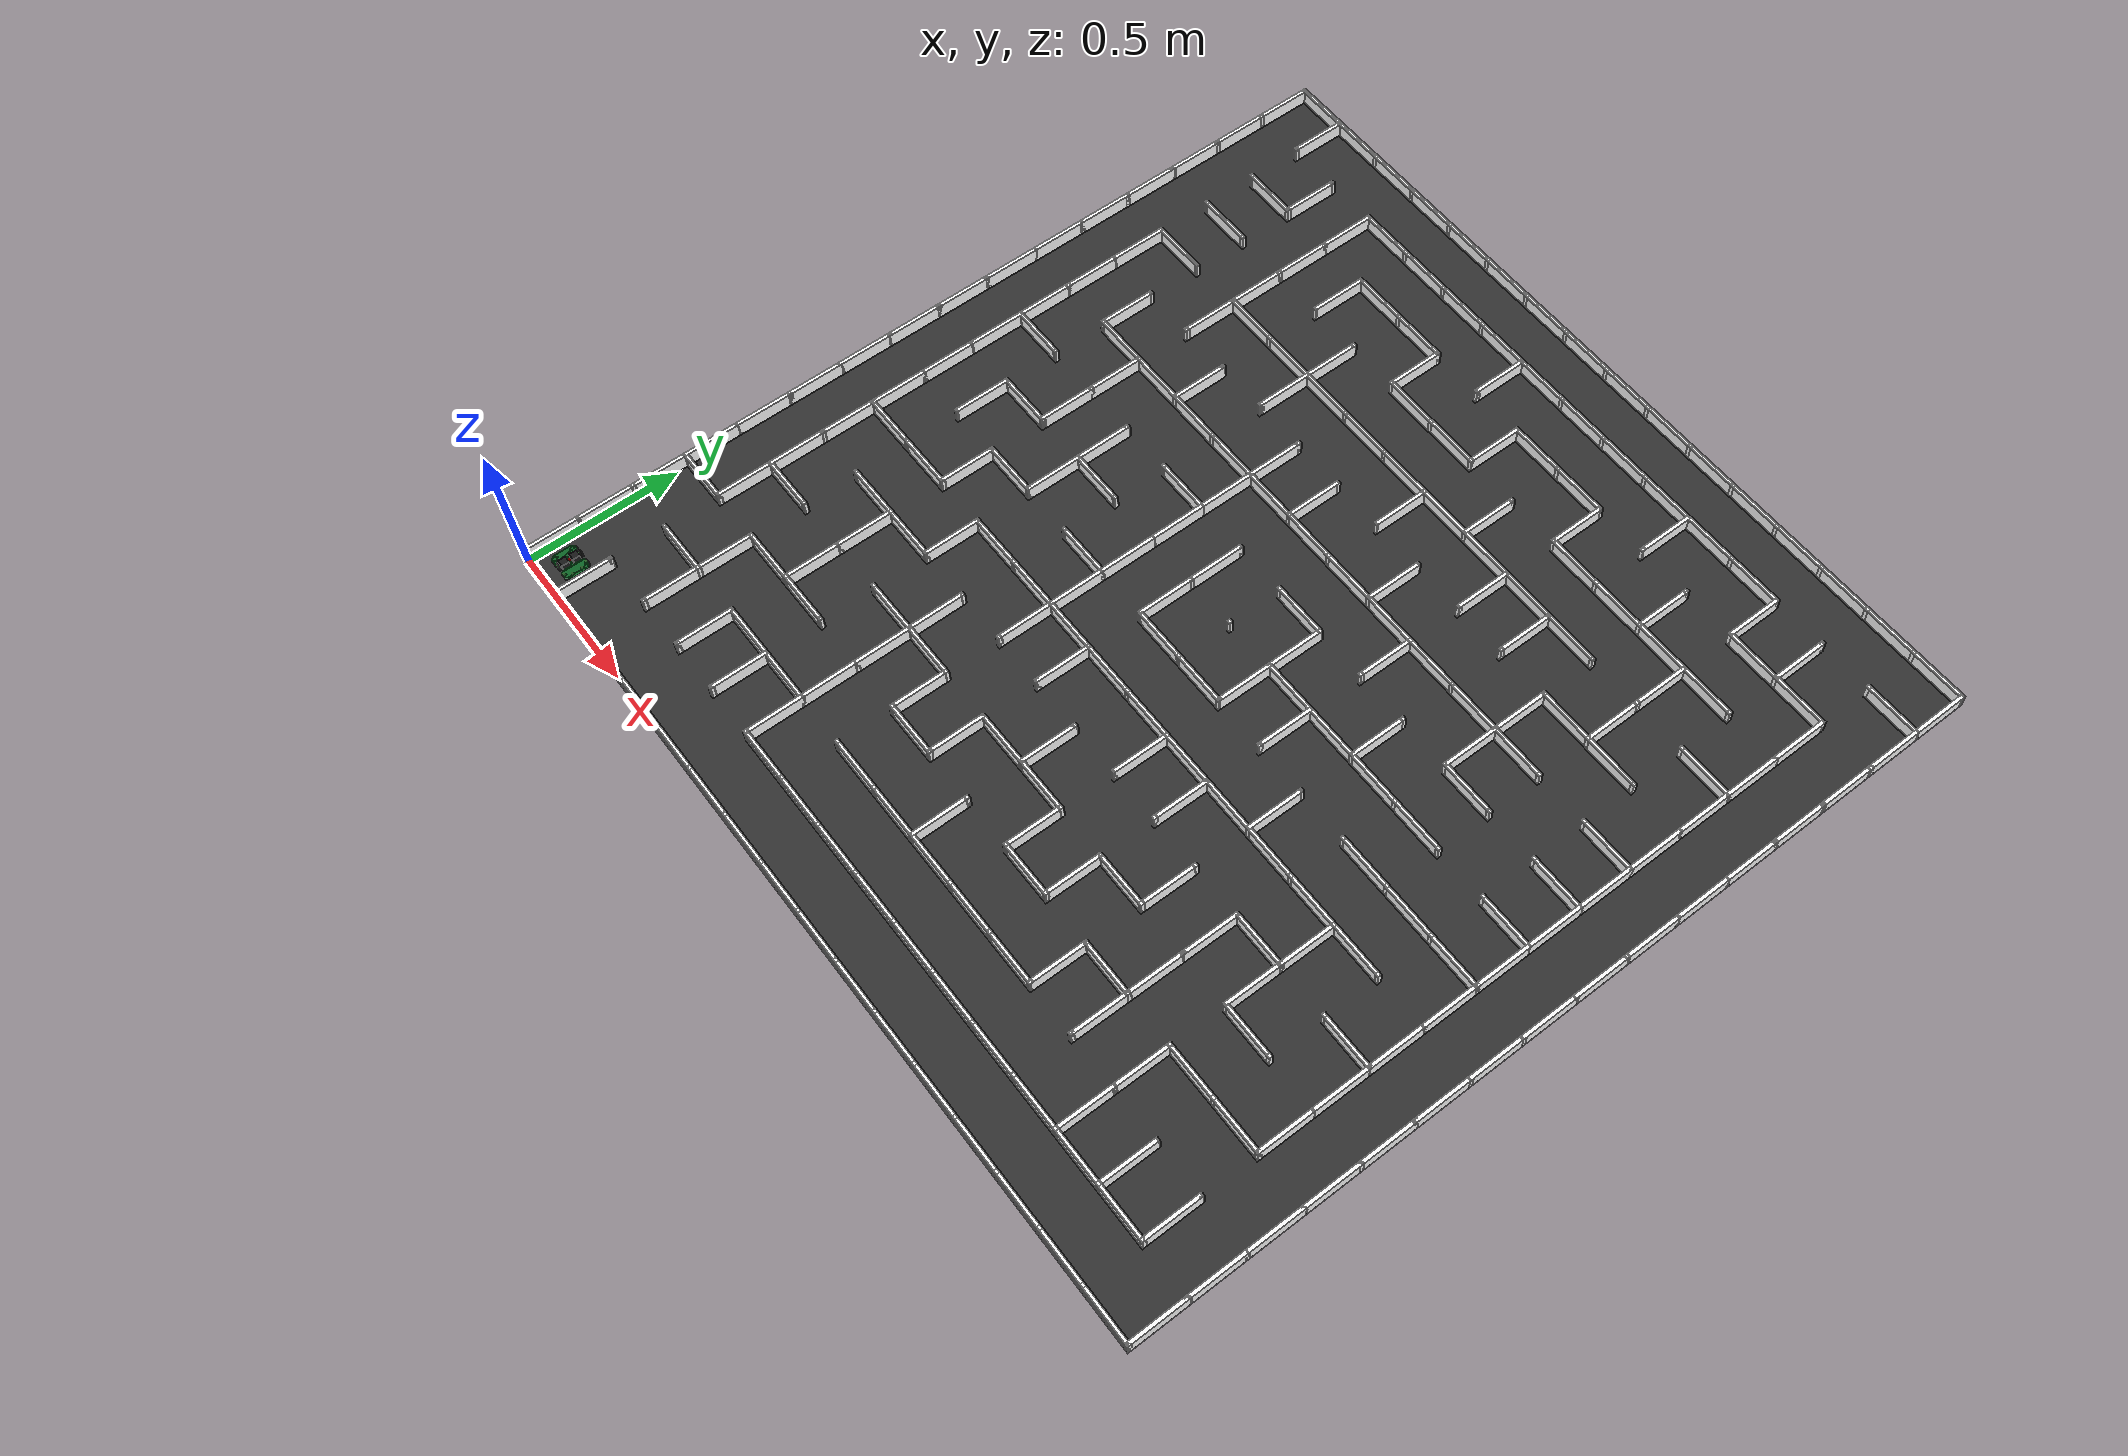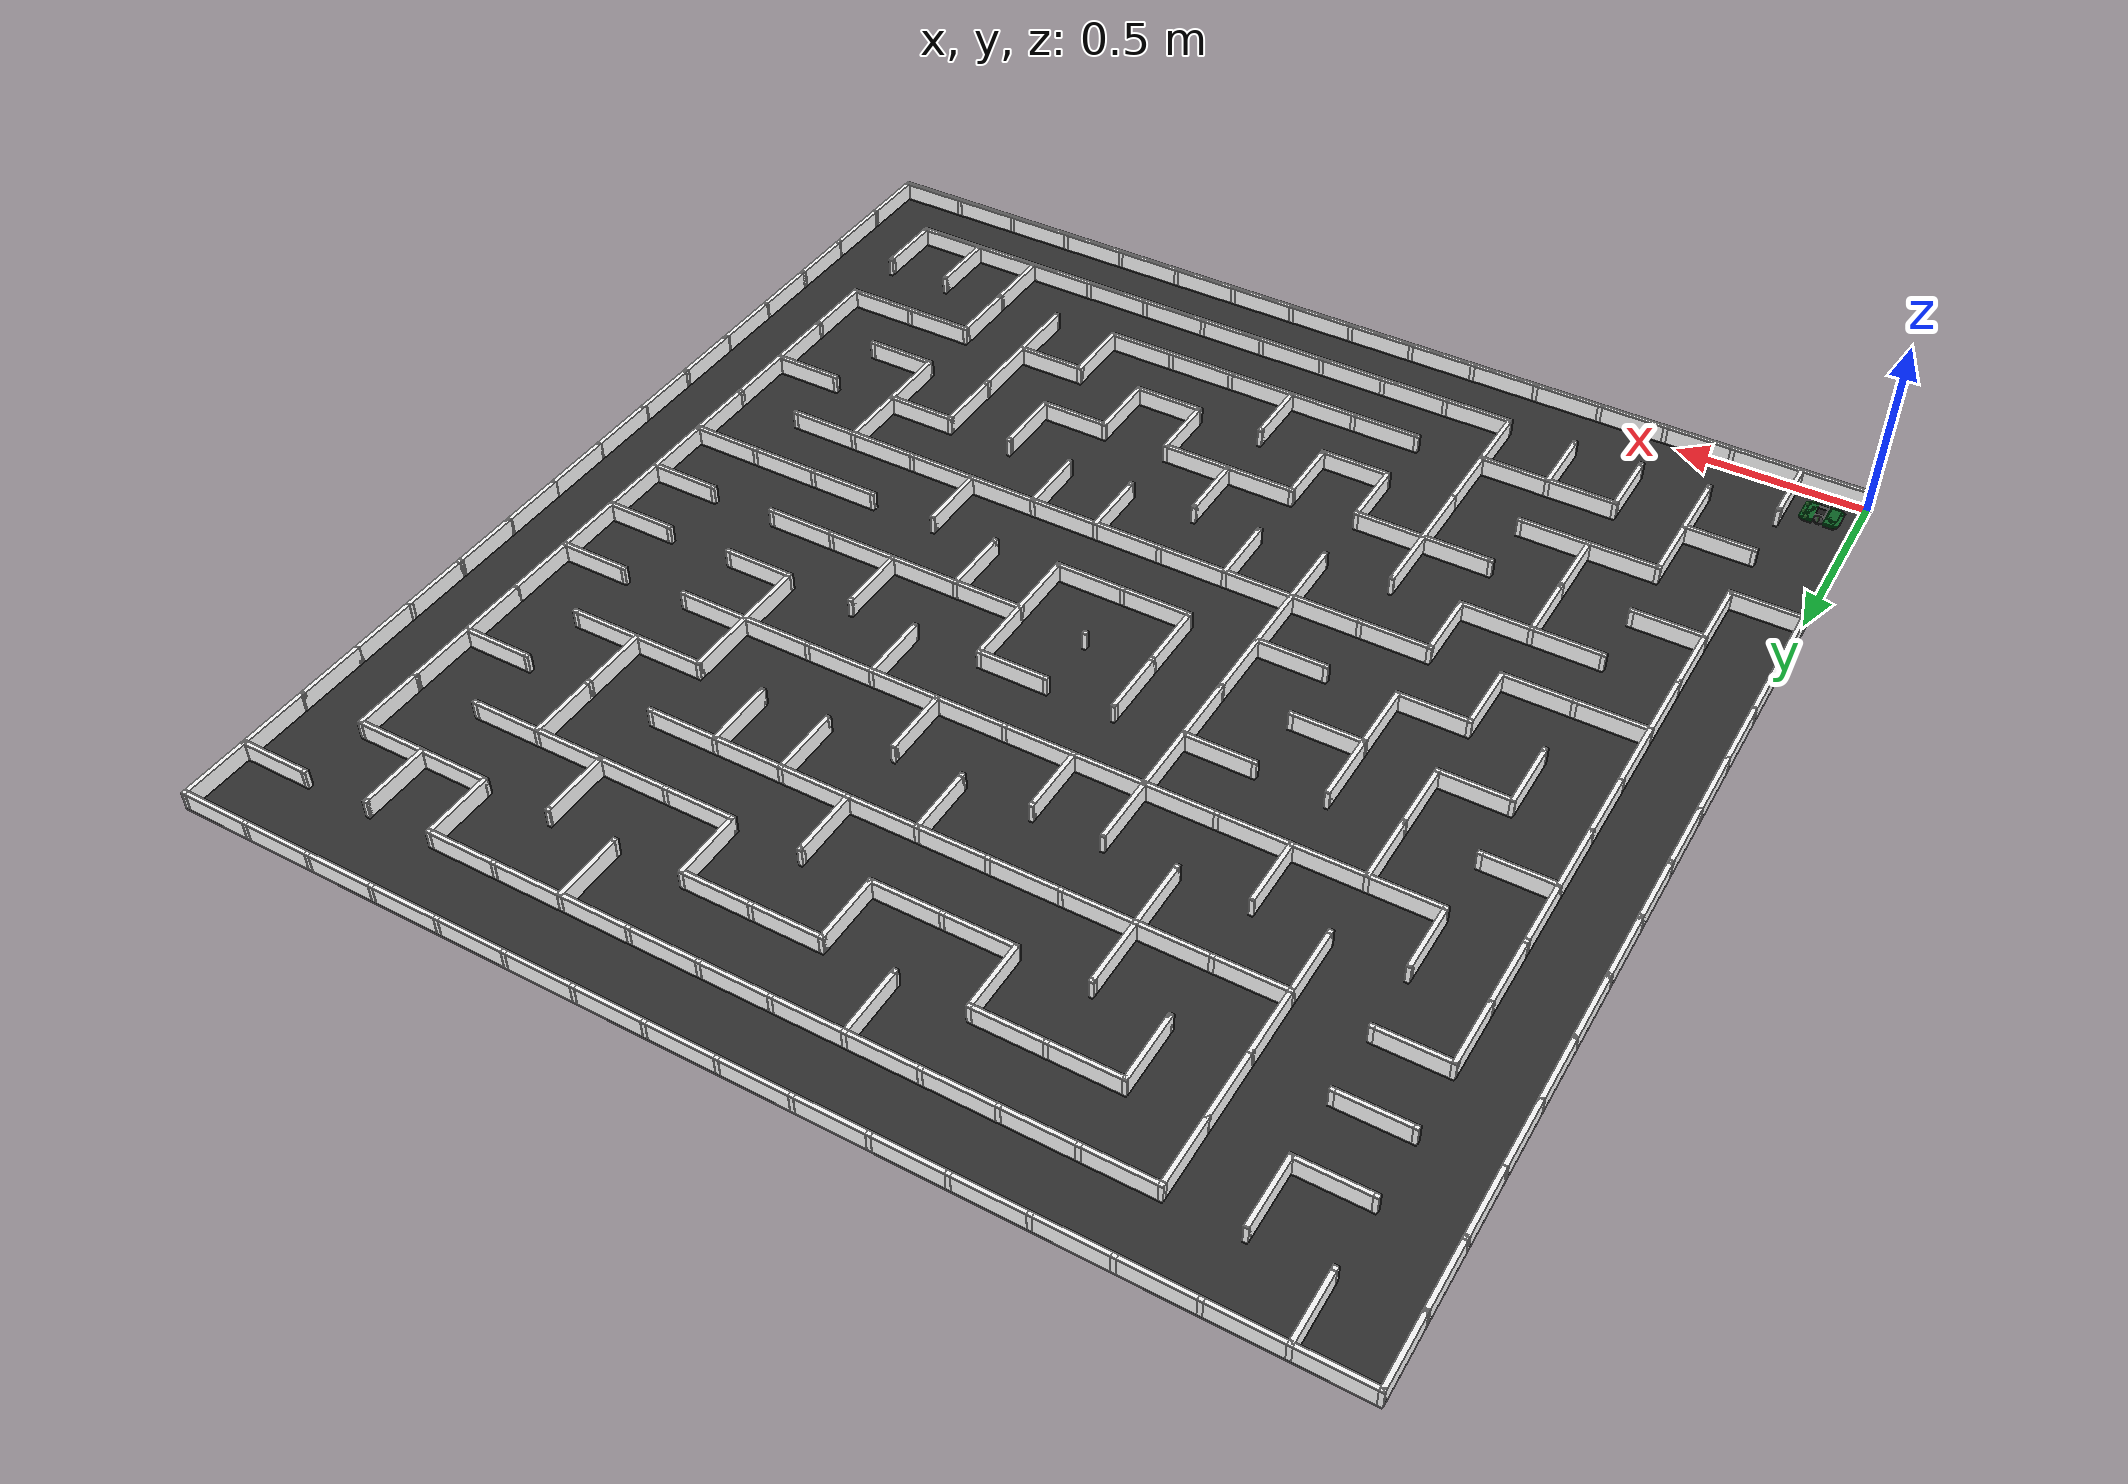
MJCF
<mujoco model="maze">
<option timestep="0.01" />
    <worldbody>
<!-- メイン光源を上から追加 -->
<light pos="0 0 3" dir="0 0 -1" diffuse="1 1 1" specular="0.5 0.5 0.5" directional="true"/>
<!-- サブ光源を複数の角度から追加 -->
<light pos="2 -2 2" dir="-1 1 -1" diffuse="0.5 0.5 0.5" specular="0.3 0.3 0.3" directional="true"/>
<light pos="-2 2 2" dir="1 -1 -1" diffuse="0.5 0.5 0.5" specular="0.3 0.3 0.3" directional="true"/>

        <body pos="0.09 0.09 0.0126" euler="0 0 0" name="mouse_body">
            <joint name='slider_x' type='slide' pos='0 0 0' axis='1 0 0'/>
            <joint name='slider_y' type='slide' pos='0 0 0' axis='0 1 0'/>
            <joint name='slider_z' type='slide' pos='0 0 0' axis='0 0 1' limited="true" range='0 0.035'/>
            <joint name="yaw" type="hinge" axis="0 0 1" limited="false" damping="0" />
            <body name="torso">
                <geom name="mein_body1" type="box" friction="0.0 0.0 0.0" size="0.05 0.03 0.0008" rgba="0.05 0.4 0.15 1" pos="0 0 0.002" mass="4.65e-3"/>
                <geom name="mein_body_chip1" type="box" friction="0.0 0.0 0.0" size="0.00707 0.00707 0.0008" rgba="0.05 0.4 0.15 1" pos="0.04 0.03 0.002" euler="0 0 45" mass="4.65e-3"/>
                <geom name="mein_body_chip2" type="box" friction="0.0 0.0 0.0" size="0.00707 0.00707 0.0008" rgba="0.05 0.4 0.15 1" pos="0.04 -0.03 0.002" euler="0 0 45" mass="4.65e-3"/>
                <geom name="mein_body_chip3" type="box" friction="0.0 0.0 0.0" size="0.00707 0.00707 0.0008" rgba="0.05 0.4 0.15 1" pos="-0.04 0.03 0.002" euler="0 0 45" mass="4.65e-3"/>
                <geom name="mein_body_chip4" type="box" friction="0.0 0.0 0.0" size="0.00707 0.00707 0.0008" rgba="0.05 0.4 0.15 1" pos="-0.04 -0.03 0.002" euler="0 0 45" mass="4.65e-3"/>
                <geom name="mein_body4" type="box" friction="0.0 0.0 0.0" size="0.013 0.04 0.0008"  rgba="0.05 0.4 0.15 1" pos="-0.027 0 0.002" mass="4.65e-3"/>
                <geom name="mein_body5" type="box" friction="0.0 0.0 0.0" size="0.013 0.04 0.0008"  rgba="0.05 0.4 0.15 1" pos="0.027 0 0.002" mass="4.65e-3"/>
                <site name="sizemiru" type="box" size="0.05 0.04 0.0008"  rgba="0.4 0.2 0.5 0" pos="0.0 0 0.00"/>
                <!--接触判定領域（この中に入ってるgeomが接触すると，センサ値としてその値を取得できる）-->
                <site name = "hit_box1" type = "box" size = "0.02 0.043 0.03" pos="0.033 0 0.0225" rgba="1 1 0 0"/>
                <site name = "hit_box2" type = "box" size = "0.06 0.08 0.03" pos="-0.0 0 0.0225" rgba="1 1 0 0"/>
            </body>

            <site name="sensor_left_front" type="box" size="0.003 0.003 0.003" pos="0.031 0.036 0.01" zaxis="1 0 0.01" rgba=".5 1 .5 1"/>
              <!-- zaxisの３つめ　0.1でちょい上向き -->
            <site name="sensor_left_side" type="box" size="0.003 0.003 0.003" pos="0.043 0.016 0.01" zaxis="0.25 1 0" rgba=".5 1 .5 1"/>
            <site name="sensor_right_front" type="box" size="0.003 0.003 0.003" pos="0.031 -0.036 0.01" zaxis="1 0 0.01" rgba=".5 1 .5 1"/>
            <site name="sensor_right_side" type="box" size="0.003 0.003 0.003" pos="0.043 -0.016 0.01" zaxis="0.25 -1 0" rgba=".5 1 .5 1"/>
            <site name="accerometer" type="sphere" size="0.001 0.001" pos="0 0 0.0"/>
            <site name="gyro" type="box" size="0.001 0.001 0.001" pos="0 0 0" />
            <site name="velocimeter" type="box" size="0.001 0.001 0.001" pos="0 0 0"/>

             <body name="left wheel" pos="-0.0 0.036 0.0135" zaxis="0 1 0">
                <joint name="left wheel joint" type="hinge" axis="0 0 1" limited="false" damping='9.6e-5' />
                <geom name="left_wheel" type="ellipsoid" size="0.0135 0.0135 0.0035" rgba=".3 .3 0.3 1" mass="5e-3"  friction="0 0 0"/>
                <site type="box" size = "0.0012 0.008 0.004" rgba=".5 1 .5 1"/>
            </body>

            <body name="right wheel" pos="-0.0 -0.036 0.0135" zaxis="0 1 0">
                <joint name="right wheel joint" type="hinge" axis="0 0 1" limited="false" damping='9.6e-5' />
                <geom name="right_wheel" type="ellipsoid" size="0.0135 0.0135 0.0035" mass="5e-3" friction="0 0 0"/> #直径27mmのタイヤ
                <site type="box" size = "0.0012 0.008 0.004" rgba=".5 1 .5 1"/>
            </body>

            <body name="motorbox1" pos="0 -0.018 0.0135" >
                <geom type="box" size="0.0117 0.0135 0.0117" rgba="0.1 0.1 0.1 1" mass="50e-3"/>
            </body>

            <body name="motorbox2" pos="0 0.018 0.0135">
                <geom type="box" size="0.0117 0.0135 0.0117" rgba="0.1 0.1 0.1 1" mass="50e-3"/>
            </body>

            <body name="core" pos="0 0 0.0135">
                <geom name="core" type="box" size="0.003 0.003 0.003" rgba="1 0 0 1" mass="50e-3"/>
            </body>

            <!--トラッキングカメラを装着-->
            <camera name="camera_name" mode="track" pos="-0.4 0 0.8" euler="0 -30 -90" fovy="60"/>
            <camera name="side_name" mode="targetbody" pos="0 0.2 0.2" euler="-40 0 180" fovy="60"/>

             <geom name="hitsafer_mein_body1" type="box" friction="0.0 0.0 0.0" size="0.05 0.03 0.015" rgba="0.05 0.4 0.15 0" pos="0 0 0.03" mass="4.65e-5"/>
                <geom name="hitsafer_mein_body_chip1" type="box" friction="0.0 0.0 0.0" size="0.00707 0.00707 0.015" rgba="0.05 0.4 0.15 0" pos="0.04 0.03 0.03" euler="0 0 45" mass="4.65e-5"/>
                <geom name="hitsafer_mein_body_chip2" type="box" friction="0.0 0.0 0.0" size="0.00707 0.00707 0.015" rgba="0.05 0.4 0.15 0" pos="0.04 -0.03 0.03" euler="0 0 45" mass="4.65e-5"/>
                <geom name="hitsafer_mein_body_chip3" type="box" friction="0.0 0.0 0.0" size="0.00707 0.00707 0.015" rgba="0.05 0.4 0.15 0" pos="-0.04 0.03 0.03" euler="0 0 45" mass="4.65e-5"/>
                <geom name="hitsafer_mein_body_chip4" type="box" friction="0.0 0.0 0.0" size="0.00707 0.00707 0.015" rgba="0.05 0.4 0.15 0" pos="-0.04 -0.03 0.03" euler="0 0 45" mass="4.65e-5"/>
                <geom name="hitsafer_mein_body4" type="box" friction="0.0 0.0 0.0" size="0.013 0.04 0.015"  rgba="0.05 0.4 0.15 0" pos="-0.027 0 0.03" mass="4.65e-5"/>
                <geom name="hitsafer_mein_body5" type="box" friction="0.0 0.0 0.0" size="0.013 0.04 0.015"  rgba="0.05 0.4 0.15 0" pos="0.027 0 0.03" mass="4.65e-5"/>

        </body>

                <!--ベース板-->
            <body name="base_plate" pos="1.44 1.44 0.015">
        <geom type="plane" mass="100" size="1.446 1.446 0.006" rgba="0.2 0.2 0.2 1" friction="0.0 0.0 0.0"/>
        </body>

        <!-- Column 1-->
        <body pos="0.0 0.0 0.037">
            <body pos="0 0 -0.0005">
                <geom type="box" mass="0.01" size="0.006 0.006 0.0245" rgba="1 1 1 1"/>
            </body>
        </body>

        <!-- Column 2-->
        <body pos="0.18 0.0 0.037">
            <body pos="0 0 -0.0005">
                <geom type="box" mass="0.01" size="0.006 0.006 0.0245" rgba="1 1 1 1"/>
            </body>
        </body>

        <!-- Column 3-->
        <body pos="0.36 0.0 0.037">
            <body pos="0 0 -0.0005">
                <geom type="box" mass="0.01" size="0.006 0.006 0.0245" rgba="1 1 1 1"/>
            </body>
        </body>

        <!-- Column 4-->
        <body pos="0.54 0.0 0.037">
            <body pos="0 0 -0.0005">
                <geom type="box" mass="0.01" size="0.006 0.006 0.0245" rgba="1 1 1 1"/>
            </body>
        </body>

        <!-- Column 5-->
        <body pos="0.72 0.0 0.037">
            <body pos="0 0 -0.0005">
                <geom type="box" mass="0.01" size="0.006 0.006 0.0245" rgba="1 1 1 1"/>
            </body>
        </body>

        <!-- Column 6-->
        <body pos="0.8999999999999999 0.0 0.037">
            <body pos="0 0 -0.0005">
                <geom type="box" mass="0.01" size="0.006 0.006 0.0245" rgba="1 1 1 1"/>
            </body>
        </body>

        <!-- Column 7-->
        <body pos="1.08 0.0 0.037">
            <body pos="0 0 -0.0005">
                <geom type="box" mass="0.01" size="0.006 0.006 0.0245" rgba="1 1 1 1"/>
            </body>
        </body>

        <!-- Column 8-->
        <body pos="1.26 0.0 0.037">
            <body pos="0 0 -0.0005">
                <geom type="box" mass="0.01" size="0.006 0.006 0.0245" rgba="1 1 1 1"/>
            </body>
        </body>

        <!-- Column 9-->
        <body pos="1.44 0.0 0.037">
            <body pos="0 0 -0.0005">
                <geom type="box" mass="0.01" size="0.006 0.006 0.0245" rgba="1 1 1 1"/>
            </body>
        </body>

        <!-- Column 10-->
        <body pos="1.6199999999999999 0.0 0.037">
            <body pos="0 0 -0.0005">
                <geom type="box" mass="0.01" size="0.006 0.006 0.0245" rgba="1 1 1 1"/>
            </body>
        </body>

        <!-- Column 11-->
        <body pos="1.7999999999999998 0.0 0.037">
            <body pos="0 0 -0.0005">
                <geom type="box" mass="0.01" size="0.006 0.006 0.0245" rgba="1 1 1 1"/>
            </body>
        </body>

        <!-- Column 12-->
        <body pos="1.98 0.0 0.037">
            <body pos="0 0 -0.0005">
                <geom type="box" mass="0.01" size="0.006 0.006 0.0245" rgba="1 1 1 1"/>
            </body>
        </body>

        <!-- Column 13-->
        <body pos="2.16 0.0 0.037">
            <body pos="0 0 -0.0005">
                <geom type="box" mass="0.01" size="0.006 0.006 0.0245" rgba="1 1 1 1"/>
            </body>
        </body>

        <!-- Column 14-->
        <body pos="2.34 0.0 0.037">
            <body pos="0 0 -0.0005">
                <geom type="box" mass="0.01" size="0.006 0.006 0.0245" rgba="1 1 1 1"/>
            </body>
        </body>

        <!-- Column 15-->
        <body pos="2.52 0.0 0.037">
            <body pos="0 0 -0.0005">
                <geom type="box" mass="0.01" size="0.006 0.006 0.0245" rgba="1 1 1 1"/>
            </body>
        </body>

        <!-- Column 16-->
        <body pos="2.6999999999999997 0.0 0.037">
            <body pos="0 0 -0.0005">
                <geom type="box" mass="0.01" size="0.006 0.006 0.0245" rgba="1 1 1 1"/>
            </body>
        </body>

        <!-- Column 17-->
        <body pos="2.88 0.0 0.037">
            <body pos="0 0 -0.0005">
                <geom type="box" mass="0.01" size="0.006 0.006 0.0245" rgba="1 1 1 1"/>
            </body>
        </body>

        <!-- Column 18-->
        <body pos="0.0 0.18 0.037">
            <body pos="0 0 -0.0005">
                <geom type="box" mass="0.01" size="0.006 0.006 0.0245" rgba="1 1 1 1"/>
            </body>
        </body>

        <!-- Column 19-->
        <body pos="0.18 0.18 0.037">
            <body pos="0 0 -0.0005">
                <geom type="box" mass="0.01" size="0.006 0.006 0.0245" rgba="1 1 1 1"/>
            </body>
        </body>

        <!-- Column 20-->
        <body pos="0.36 0.18 0.037">
            <body pos="0 0 -0.0005">
                <geom type="box" mass="0.01" size="0.006 0.006 0.0245" rgba="1 1 1 1"/>
            </body>
        </body>

        <!-- Column 21-->
        <body pos="0.54 0.18 0.037">
            <body pos="0 0 -0.0005">
                <geom type="box" mass="0.01" size="0.006 0.006 0.0245" rgba="1 1 1 1"/>
            </body>
        </body>

        <!-- Column 22-->
        <body pos="0.72 0.18 0.037">
            <body pos="0 0 -0.0005">
                <geom type="box" mass="0.01" size="0.006 0.006 0.0245" rgba="1 1 1 1"/>
            </body>
        </body>

        <!-- Column 23-->
        <body pos="0.8999999999999999 0.18 0.037">
            <body pos="0 0 -0.0005">
                <geom type="box" mass="0.01" size="0.006 0.006 0.0245" rgba="1 1 1 1"/>
            </body>
        </body>

        <!-- Column 24-->
        <body pos="1.08 0.18 0.037">
            <body pos="0 0 -0.0005">
                <geom type="box" mass="0.01" size="0.006 0.006 0.0245" rgba="1 1 1 1"/>
            </body>
        </body>

        <!-- Column 25-->
        <body pos="1.26 0.18 0.037">
            <body pos="0 0 -0.0005">
                <geom type="box" mass="0.01" size="0.006 0.006 0.0245" rgba="1 1 1 1"/>
            </body>
        </body>

        <!-- Column 26-->
        <body pos="1.44 0.18 0.037">
            <body pos="0 0 -0.0005">
                <geom type="box" mass="0.01" size="0.006 0.006 0.0245" rgba="1 1 1 1"/>
            </body>
        </body>

        <!-- Column 27-->
        <body pos="1.6199999999999999 0.18 0.037">
            <body pos="0 0 -0.0005">
                <geom type="box" mass="0.01" size="0.006 0.006 0.0245" rgba="1 1 1 1"/>
            </body>
        </body>

        <!-- Column 28-->
        <body pos="1.7999999999999998 0.18 0.037">
            <body pos="0 0 -0.0005">
                <geom type="box" mass="0.01" size="0.006 0.006 0.0245" rgba="1 1 1 1"/>
            </body>
        </body>

        <!-- Column 29-->
        <body pos="1.98 0.18 0.037">
            <body pos="0 0 -0.0005">
                <geom type="box" mass="0.01" size="0.006 0.006 0.0245" rgba="1 1 1 1"/>
            </body>
        </body>

        <!-- Column 30-->
        <body pos="2.16 0.18 0.037">
            <body pos="0 0 -0.0005">
                <geom type="box" mass="0.01" size="0.006 0.006 0.0245" rgba="1 1 1 1"/>
            </body>
        </body>

        <!-- Column 31-->
        <body pos="2.34 0.18 0.037">
            <body pos="0 0 -0.0005">
                <geom type="box" mass="0.01" size="0.006 0.006 0.0245" rgba="1 1 1 1"/>
            </body>
        </body>

        <!-- Column 32-->
        <body pos="2.52 0.18 0.037">
            <body pos="0 0 -0.0005">
                <geom type="box" mass="0.01" size="0.006 0.006 0.0245" rgba="1 1 1 1"/>
            </body>
        </body>

        <!-- Column 33-->
        <body pos="2.6999999999999997 0.18 0.037">
            <body pos="0 0 -0.0005">
                <geom type="box" mass="0.01" size="0.006 0.006 0.0245" rgba="1 1 1 1"/>
            </body>
        </body>

        <!-- Column 34-->
        <body pos="2.88 0.18 0.037">
            <body pos="0 0 -0.0005">
                <geom type="box" mass="0.01" size="0.006 0.006 0.0245" rgba="1 1 1 1"/>
            </body>
        </body>

        <!-- Column 35-->
        <body pos="0.0 0.36 0.037">
            <body pos="0 0 -0.0005">
                <geom type="box" mass="0.01" size="0.006 0.006 0.0245" rgba="1 1 1 1"/>
            </body>
        </body>

        <!-- Column 36-->
        <body pos="0.18 0.36 0.037">
            <body pos="0 0 -0.0005">
                <geom type="box" mass="0.01" size="0.006 0.006 0.0245" rgba="1 1 1 1"/>
            </body>
        </body>

        <!-- Column 37-->
        <body pos="0.36 0.36 0.037">
            <body pos="0 0 -0.0005">
                <geom type="box" mass="0.01" size="0.006 0.006 0.0245" rgba="1 1 1 1"/>
            </body>
        </body>

        <!-- Column 38-->
        <body pos="0.54 0.36 0.037">
            <body pos="0 0 -0.0005">
                <geom type="box" mass="0.01" size="0.006 0.006 0.0245" rgba="1 1 1 1"/>
            </body>
        </body>

        <!-- Column 39-->
        <body pos="0.72 0.36 0.037">
            <body pos="0 0 -0.0005">
                <geom type="box" mass="0.01" size="0.006 0.006 0.0245" rgba="1 1 1 1"/>
            </body>
        </body>

        <!-- Column 40-->
        <body pos="0.8999999999999999 0.36 0.037">
            <body pos="0 0 -0.0005">
                <geom type="box" mass="0.01" size="0.006 0.006 0.0245" rgba="1 1 1 1"/>
            </body>
        </body>

        <!-- Column 41-->
        <body pos="1.08 0.36 0.037">
            <body pos="0 0 -0.0005">
                <geom type="box" mass="0.01" size="0.006 0.006 0.0245" rgba="1 1 1 1"/>
            </body>
        </body>

        <!-- Column 42-->
        <body pos="1.26 0.36 0.037">
            <body pos="0 0 -0.0005">
                <geom type="box" mass="0.01" size="0.006 0.006 0.0245" rgba="1 1 1 1"/>
            </body>
        </body>

        <!-- Column 43-->
        <body pos="1.44 0.36 0.037">
            <body pos="0 0 -0.0005">
                <geom type="box" mass="0.01" size="0.006 0.006 0.0245" rgba="1 1 1 1"/>
            </body>
        </body>

        <!-- Column 44-->
        <body pos="1.6199999999999999 0.36 0.037">
            <body pos="0 0 -0.0005">
                <geom type="box" mass="0.01" size="0.006 0.006 0.0245" rgba="1 1 1 1"/>
            </body>
        </body>

        <!-- Column 45-->
        <body pos="1.7999999999999998 0.36 0.037">
            <body pos="0 0 -0.0005">
                <geom type="box" mass="0.01" size="0.006 0.006 0.0245" rgba="1 1 1 1"/>
            </body>
        </body>

        <!-- Column 46-->
        <body pos="1.98 0.36 0.037">
            <body pos="0 0 -0.0005">
                <geom type="box" mass="0.01" size="0.006 0.006 0.0245" rgba="1 1 1 1"/>
            </body>
        </body>

        <!-- Column 47-->
        <body pos="2.16 0.36 0.037">
            <body pos="0 0 -0.0005">
                <geom type="box" mass="0.01" size="0.006 0.006 0.0245" rgba="1 1 1 1"/>
            </body>
        </body>

        <!-- Column 48-->
        <body pos="2.34 0.36 0.037">
            <body pos="0 0 -0.0005">
                <geom type="box" mass="0.01" size="0.006 0.006 0.0245" rgba="1 1 1 1"/>
            </body>
        </body>

        <!-- Column 49-->
        <body pos="2.52 0.36 0.037">
            <body pos="0 0 -0.0005">
                <geom type="box" mass="0.01" size="0.006 0.006 0.0245" rgba="1 1 1 1"/>
            </body>
        </body>

        <!-- Column 50-->
        <body pos="2.6999999999999997 0.36 0.037">
            <body pos="0 0 -0.0005">
                <geom type="box" mass="0.01" size="0.006 0.006 0.0245" rgba="1 1 1 1"/>
            </body>
        </body>

        <!-- Column 51-->
        <body pos="2.88 0.36 0.037">
            <body pos="0 0 -0.0005">
                <geom type="box" mass="0.01" size="0.006 0.006 0.0245" rgba="1 1 1 1"/>
            </body>
        </body>

        <!-- Column 52-->
        <body pos="0.0 0.54 0.037">
            <body pos="0 0 -0.0005">
                <geom type="box" mass="0.01" size="0.006 0.006 0.0245" rgba="1 1 1 1"/>
            </body>
        </body>

        <!-- Column 53-->
        <body pos="0.18 0.54 0.037">
            <body pos="0 0 -0.0005">
                <geom type="box" mass="0.01" size="0.006 0.006 0.0245" rgba="1 1 1 1"/>
            </body>
        </body>

        <!-- Column 54-->
        <body pos="0.36 0.54 0.037">
            <body pos="0 0 -0.0005">
                <geom type="box" mass="0.01" size="0.006 0.006 0.0245" rgba="1 1 1 1"/>
            </body>
        </body>

        <!-- Column 55-->
        <body pos="0.54 0.54 0.037">
            <body pos="0 0 -0.0005">
                <geom type="box" mass="0.01" size="0.006 0.006 0.0245" rgba="1 1 1 1"/>
            </body>
        </body>

        <!-- Column 56-->
        <body pos="0.72 0.54 0.037">
            <body pos="0 0 -0.0005">
                <geom type="box" mass="0.01" size="0.006 0.006 0.0245" rgba="1 1 1 1"/>
            </body>
        </body>

        <!-- Column 57-->
        <body pos="0.8999999999999999 0.54 0.037">
            <body pos="0 0 -0.0005">
                <geom type="box" mass="0.01" size="0.006 0.006 0.0245" rgba="1 1 1 1"/>
            </body>
        </body>

        <!-- Column 58-->
        <body pos="1.08 0.54 0.037">
            <body pos="0 0 -0.0005">
                <geom type="box" mass="0.01" size="0.006 0.006 0.0245" rgba="1 1 1 1"/>
            </body>
        </body>

        <!-- Column 59-->
        <body pos="1.26 0.54 0.037">
            <body pos="0 0 -0.0005">
                <geom type="box" mass="0.01" size="0.006 0.006 0.0245" rgba="1 1 1 1"/>
            </body>
        </body>

        <!-- Column 60-->
        <body pos="1.44 0.54 0.037">
            <body pos="0 0 -0.0005">
                <geom type="box" mass="0.01" size="0.006 0.006 0.0245" rgba="1 1 1 1"/>
            </body>
        </body>

        <!-- Column 61-->
        <body pos="1.6199999999999999 0.54 0.037">
            <body pos="0 0 -0.0005">
                <geom type="box" mass="0.01" size="0.006 0.006 0.0245" rgba="1 1 1 1"/>
            </body>
        </body>

        <!-- Column 62-->
        <body pos="1.7999999999999998 0.54 0.037">
            <body pos="0 0 -0.0005">
                <geom type="box" mass="0.01" size="0.006 0.006 0.0245" rgba="1 1 1 1"/>
            </body>
        </body>

        <!-- Column 63-->
        <body pos="1.98 0.54 0.037">
            <body pos="0 0 -0.0005">
                <geom type="box" mass="0.01" size="0.006 0.006 0.0245" rgba="1 1 1 1"/>
            </body>
        </body>

        <!-- Column 64-->
        <body pos="2.16 0.54 0.037">
            <body pos="0 0 -0.0005">
                <geom type="box" mass="0.01" size="0.006 0.006 0.0245" rgba="1 1 1 1"/>
            </body>
        </body>

        <!-- Column 65-->
        <body pos="2.34 0.54 0.037">
            <body pos="0 0 -0.0005">
                <geom type="box" mass="0.01" size="0.006 0.006 0.0245" rgba="1 1 1 1"/>
            </body>
        </body>

        <!-- Column 66-->
        <body pos="2.52 0.54 0.037">
            <body pos="0 0 -0.0005">
                <geom type="box" mass="0.01" size="0.006 0.006 0.0245" rgba="1 1 1 1"/>
            </body>
        </body>

        <!-- Column 67-->
        <body pos="2.6999999999999997 0.54 0.037">
            <body pos="0 0 -0.0005">
                <geom type="box" mass="0.01" size="0.006 0.006 0.0245" rgba="1 1 1 1"/>
            </body>
        </body>

        <!-- Column 68-->
        <body pos="2.88 0.54 0.037">
            <body pos="0 0 -0.0005">
                <geom type="box" mass="0.01" size="0.006 0.006 0.0245" rgba="1 1 1 1"/>
            </body>
        </body>

        <!-- Column 69-->
        <body pos="0.0 0.72 0.037">
            <body pos="0 0 -0.0005">
                <geom type="box" mass="0.01" size="0.006 0.006 0.0245" rgba="1 1 1 1"/>
            </body>
        </body>

        <!-- Column 70-->
        <body pos="0.18 0.72 0.037">
            <body pos="0 0 -0.0005">
                <geom type="box" mass="0.01" size="0.006 0.006 0.0245" rgba="1 1 1 1"/>
            </body>
        </body>

        <!-- Column 71-->
        <body pos="0.36 0.72 0.037">
            <body pos="0 0 -0.0005">
                <geom type="box" mass="0.01" size="0.006 0.006 0.0245" rgba="1 1 1 1"/>
            </body>
        </body>

        <!-- Column 72-->
        <body pos="0.54 0.72 0.037">
            <body pos="0 0 -0.0005">
                <geom type="box" mass="0.01" size="0.006 0.006 0.0245" rgba="1 1 1 1"/>
            </body>
        </body>

        <!-- Column 73-->
        <body pos="0.72 0.72 0.037">
            <body pos="0 0 -0.0005">
                <geom type="box" mass="0.01" size="0.006 0.006 0.0245" rgba="1 1 1 1"/>
            </body>
        </body>

        <!-- Column 74-->
        <body pos="0.8999999999999999 0.72 0.037">
            <body pos="0 0 -0.0005">
                <geom type="box" mass="0.01" size="0.006 0.006 0.0245" rgba="1 1 1 1"/>
            </body>
        </body>

        <!-- Column 75-->
        <body pos="1.08 0.72 0.037">
            <body pos="0 0 -0.0005">
                <geom type="box" mass="0.01" size="0.006 0.006 0.0245" rgba="1 1 1 1"/>
            </body>
        </body>

        <!-- Column 76-->
        <body pos="1.26 0.72 0.037">
            <body pos="0 0 -0.0005">
                <geom type="box" mass="0.01" size="0.006 0.006 0.0245" rgba="1 1 1 1"/>
            </body>
        </body>

        <!-- Column 77-->
        <body pos="1.44 0.72 0.037">
            <body pos="0 0 -0.0005">
                <geom type="box" mass="0.01" size="0.006 0.006 0.0245" rgba="1 1 1 1"/>
            </body>
        </body>

        <!-- Column 78-->
        <body pos="1.6199999999999999 0.72 0.037">
            <body pos="0 0 -0.0005">
                <geom type="box" mass="0.01" size="0.006 0.006 0.0245" rgba="1 1 1 1"/>
            </body>
        </body>

        <!-- Column 79-->
        <body pos="1.7999999999999998 0.72 0.037">
            <body pos="0 0 -0.0005">
                <geom type="box" mass="0.01" size="0.006 0.006 0.0245" rgba="1 1 1 1"/>
            </body>
        </body>

        <!-- Column 80-->
        <body pos="1.98 0.72 0.037">
            <body pos="0 0 -0.0005">
                <geom type="box" mass="0.01" size="0.006 0.006 0.0245" rgba="1 1 1 1"/>
            </body>
        </body>

        <!-- Column 81-->
        <body pos="2.16 0.72 0.037">
            <body pos="0 0 -0.0005">
                <geom type="box" mass="0.01" size="0.006 0.006 0.0245" rgba="1 1 1 1"/>
            </body>
        </body>

        <!-- Column 82-->
        <body pos="2.34 0.72 0.037">
            <body pos="0 0 -0.0005">
                <geom type="box" mass="0.01" size="0.006 0.006 0.0245" rgba="1 1 1 1"/>
            </body>
        </body>

        <!-- Column 83-->
        <body pos="2.52 0.72 0.037">
            <body pos="0 0 -0.0005">
                <geom type="box" mass="0.01" size="0.006 0.006 0.0245" rgba="1 1 1 1"/>
            </body>
        </body>

        <!-- Column 84-->
        <body pos="2.6999999999999997 0.72 0.037">
            <body pos="0 0 -0.0005">
                <geom type="box" mass="0.01" size="0.006 0.006 0.0245" rgba="1 1 1 1"/>
            </body>
        </body>

        <!-- Column 85-->
        <body pos="2.88 0.72 0.037">
            <body pos="0 0 -0.0005">
                <geom type="box" mass="0.01" size="0.006 0.006 0.0245" rgba="1 1 1 1"/>
            </body>
        </body>

        <!-- Column 86-->
        <body pos="0.0 0.8999999999999999 0.037">
            <body pos="0 0 -0.0005">
                <geom type="box" mass="0.01" size="0.006 0.006 0.0245" rgba="1 1 1 1"/>
            </body>
        </body>

        <!-- Column 87-->
        <body pos="0.18 0.8999999999999999 0.037">
            <body pos="0 0 -0.0005">
                <geom type="box" mass="0.01" size="0.006 0.006 0.0245" rgba="1 1 1 1"/>
            </body>
        </body>

        <!-- Column 88-->
        <body pos="0.36 0.8999999999999999 0.037">
            <body pos="0 0 -0.0005">
                <geom type="box" mass="0.01" size="0.006 0.006 0.0245" rgba="1 1 1 1"/>
            </body>
        </body>

        <!-- Column 89-->
        <body pos="0.54 0.8999999999999999 0.037">
            <body pos="0 0 -0.0005">
                <geom type="box" mass="0.01" size="0.006 0.006 0.0245" rgba="1 1 1 1"/>
            </body>
        </body>

        <!-- Column 90-->
        <body pos="0.72 0.8999999999999999 0.037">
            <body pos="0 0 -0.0005">
                <geom type="box" mass="0.01" size="0.006 0.006 0.0245" rgba="1 1 1 1"/>
            </body>
        </body>

        <!-- Column 91-->
        <body pos="0.8999999999999999 0.8999999999999999 0.037">
            <body pos="0 0 -0.0005">
                <geom type="box" mass="0.01" size="0.006 0.006 0.0245" rgba="1 1 1 1"/>
            </body>
        </body>

        <!-- Column 92-->
        <body pos="1.08 0.8999999999999999 0.037">
            <body pos="0 0 -0.0005">
                <geom type="box" mass="0.01" size="0.006 0.006 0.0245" rgba="1 1 1 1"/>
            </body>
        </body>

        <!-- Column 93-->
        <body pos="1.26 0.8999999999999999 0.037">
            <body pos="0 0 -0.0005">
                <geom type="box" mass="0.01" size="0.006 0.006 0.0245" rgba="1 1 1 1"/>
            </body>
        </body>

        <!-- Column 94-->
        <body pos="1.44 0.8999999999999999 0.037">
            <body pos="0 0 -0.0005">
                <geom type="box" mass="0.01" size="0.006 0.006 0.0245" rgba="1 1 1 1"/>
            </body>
        </body>

        <!-- Column 95-->
        <body pos="1.6199999999999999 0.8999999999999999 0.037">
            <body pos="0 0 -0.0005">
                <geom type="box" mass="0.01" size="0.006 0.006 0.0245" rgba="1 1 1 1"/>
            </body>
        </body>

        <!-- Column 96-->
        <body pos="1.7999999999999998 0.8999999999999999 0.037">
            <body pos="0 0 -0.0005">
                <geom type="box" mass="0.01" size="0.006 0.006 0.0245" rgba="1 1 1 1"/>
            </body>
        </body>

        <!-- Column 97-->
        <body pos="1.98 0.8999999999999999 0.037">
            <body pos="0 0 -0.0005">
                <geom type="box" mass="0.01" size="0.006 0.006 0.0245" rgba="1 1 1 1"/>
            </body>
        </body>

        <!-- Column 98-->
        <body pos="2.16 0.8999999999999999 0.037">
            <body pos="0 0 -0.0005">
                <geom type="box" mass="0.01" size="0.006 0.006 0.0245" rgba="1 1 1 1"/>
            </body>
        </body>

        <!-- Column 99-->
        <body pos="2.34 0.8999999999999999 0.037">
            <body pos="0 0 -0.0005">
                <geom type="box" mass="0.01" size="0.006 0.006 0.0245" rgba="1 1 1 1"/>
            </body>
        </body>

        <!-- Column 100-->
        <body pos="2.52 0.8999999999999999 0.037">
            <body pos="0 0 -0.0005">
                <geom type="box" mass="0.01" size="0.006 0.006 0.0245" rgba="1 1 1 1"/>
            </body>
        </body>

        <!-- Column 101-->
        <body pos="2.6999999999999997 0.8999999999999999 0.037">
            <body pos="0 0 -0.0005">
                <geom type="box" mass="0.01" size="0.006 0.006 0.0245" rgba="1 1 1 1"/>
            </body>
        </body>

        <!-- Column 102-->
        <body pos="2.88 0.8999999999999999 0.037">
            <body pos="0 0 -0.0005">
                <geom type="box" mass="0.01" size="0.006 0.006 0.0245" rgba="1 1 1 1"/>
            </body>
        </body>

        <!-- Column 103-->
        <body pos="0.0 1.08 0.037">
            <body pos="0 0 -0.0005">
                <geom type="box" mass="0.01" size="0.006 0.006 0.0245" rgba="1 1 1 1"/>
            </body>
        </body>

        <!-- Column 104-->
        <body pos="0.18 1.08 0.037">
            <body pos="0 0 -0.0005">
                <geom type="box" mass="0.01" size="0.006 0.006 0.0245" rgba="1 1 1 1"/>
            </body>
        </body>

        <!-- Column 105-->
        <body pos="0.36 1.08 0.037">
            <body pos="0 0 -0.0005">
                <geom type="box" mass="0.01" size="0.006 0.006 0.0245" rgba="1 1 1 1"/>
            </body>
        </body>

        <!-- Column 106-->
        <body pos="0.54 1.08 0.037">
            <body pos="0 0 -0.0005">
                <geom type="box" mass="0.01" size="0.006 0.006 0.0245" rgba="1 1 1 1"/>
            </body>
        </body>

        <!-- Column 107-->
        <body pos="0.72 1.08 0.037">
            <body pos="0 0 -0.0005">
                <geom type="box" mass="0.01" size="0.006 0.006 0.0245" rgba="1 1 1 1"/>
            </body>
        </body>

        <!-- Column 108-->
        <body pos="0.8999999999999999 1.08 0.037">
            <body pos="0 0 -0.0005">
                <geom type="box" mass="0.01" size="0.006 0.006 0.0245" rgba="1 1 1 1"/>
            </body>
        </body>

        <!-- Column 109-->
        <body pos="1.08 1.08 0.037">
            <body pos="0 0 -0.0005">
                <geom type="box" mass="0.01" size="0.006 0.006 0.0245" rgba="1 1 1 1"/>
            </body>
        </body>

        <!-- Column 110-->
        <body pos="1.26 1.08 0.037">
            <body pos="0 0 -0.0005">
                <geom type="box" mass="0.01" size="0.006 0.006 0.0245" rgba="1 1 1 1"/>
            </body>
        </body>

        <!-- Column 111-->
        <body pos="1.44 1.08 0.037">
            <body pos="0 0 -0.0005">
                <geom type="box" mass="0.01" size="0.006 0.006 0.0245" rgba="1 1 1 1"/>
            </body>
        </body>

        <!-- Column 112-->
        <body pos="1.6199999999999999 1.08 0.037">
            <body pos="0 0 -0.0005">
                <geom type="box" mass="0.01" size="0.006 0.006 0.0245" rgba="1 1 1 1"/>
            </body>
        </body>

        <!-- Column 113-->
        <body pos="1.7999999999999998 1.08 0.037">
            <body pos="0 0 -0.0005">
                <geom type="box" mass="0.01" size="0.006 0.006 0.0245" rgba="1 1 1 1"/>
            </body>
        </body>

        <!-- Column 114-->
        <body pos="1.98 1.08 0.037">
            <body pos="0 0 -0.0005">
                <geom type="box" mass="0.01" size="0.006 0.006 0.0245" rgba="1 1 1 1"/>
            </body>
        </body>

        <!-- Column 115-->
        <body pos="2.16 1.08 0.037">
            <body pos="0 0 -0.0005">
                <geom type="box" mass="0.01" size="0.006 0.006 0.0245" rgba="1 1 1 1"/>
            </body>
        </body>

        <!-- Column 116-->
        <body pos="2.34 1.08 0.037">
            <body pos="0 0 -0.0005">
                <geom type="box" mass="0.01" size="0.006 0.006 0.0245" rgba="1 1 1 1"/>
            </body>
        </body>

        <!-- Column 117-->
        <body pos="2.52 1.08 0.037">
            <body pos="0 0 -0.0005">
                <geom type="box" mass="0.01" size="0.006 0.006 0.0245" rgba="1 1 1 1"/>
            </body>
        </body>

        <!-- Column 118-->
        <body pos="2.6999999999999997 1.08 0.037">
            <body pos="0 0 -0.0005">
                <geom type="box" mass="0.01" size="0.006 0.006 0.0245" rgba="1 1 1 1"/>
            </body>
        </body>

        <!-- Column 119-->
        <body pos="2.88 1.08 0.037">
            <body pos="0 0 -0.0005">
                <geom type="box" mass="0.01" size="0.006 0.006 0.0245" rgba="1 1 1 1"/>
            </body>
        </body>

        <!-- Column 120-->
        <body pos="0.0 1.26 0.037">
            <body pos="0 0 -0.0005">
                <geom type="box" mass="0.01" size="0.006 0.006 0.0245" rgba="1 1 1 1"/>
            </body>
        </body>

        <!-- Column 121-->
        <body pos="0.18 1.26 0.037">
            <body pos="0 0 -0.0005">
                <geom type="box" mass="0.01" size="0.006 0.006 0.0245" rgba="1 1 1 1"/>
            </body>
        </body>

        <!-- Column 122-->
        <body pos="0.36 1.26 0.037">
            <body pos="0 0 -0.0005">
                <geom type="box" mass="0.01" size="0.006 0.006 0.0245" rgba="1 1 1 1"/>
            </body>
        </body>

        <!-- Column 123-->
        <body pos="0.54 1.26 0.037">
            <body pos="0 0 -0.0005">
                <geom type="box" mass="0.01" size="0.006 0.006 0.0245" rgba="1 1 1 1"/>
            </body>
        </body>

        <!-- Column 124-->
        <body pos="0.72 1.26 0.037">
            <body pos="0 0 -0.0005">
                <geom type="box" mass="0.01" size="0.006 0.006 0.0245" rgba="1 1 1 1"/>
            </body>
        </body>

        <!-- Column 125-->
        <body pos="0.8999999999999999 1.26 0.037">
            <body pos="0 0 -0.0005">
                <geom type="box" mass="0.01" size="0.006 0.006 0.0245" rgba="1 1 1 1"/>
            </body>
        </body>

        <!-- Column 126-->
        <body pos="1.08 1.26 0.037">
            <body pos="0 0 -0.0005">
                <geom type="box" mass="0.01" size="0.006 0.006 0.0245" rgba="1 1 1 1"/>
            </body>
        </body>

        <!-- Column 127-->
        <body pos="1.26 1.26 0.037">
            <body pos="0 0 -0.0005">
                <geom type="box" mass="0.01" size="0.006 0.006 0.0245" rgba="1 1 1 1"/>
            </body>
        </body>

        <!-- Column 128-->
        <body pos="1.44 1.26 0.037">
            <body pos="0 0 -0.0005">
                <geom type="box" mass="0.01" size="0.006 0.006 0.0245" rgba="1 1 1 1"/>
            </body>
        </body>

        <!-- Column 129-->
        <body pos="1.6199999999999999 1.26 0.037">
            <body pos="0 0 -0.0005">
                <geom type="box" mass="0.01" size="0.006 0.006 0.0245" rgba="1 1 1 1"/>
            </body>
        </body>

        <!-- Column 130-->
        <body pos="1.7999999999999998 1.26 0.037">
            <body pos="0 0 -0.0005">
                <geom type="box" mass="0.01" size="0.006 0.006 0.0245" rgba="1 1 1 1"/>
            </body>
        </body>

        <!-- Column 131-->
        <body pos="1.98 1.26 0.037">
            <body pos="0 0 -0.0005">
                <geom type="box" mass="0.01" size="0.006 0.006 0.0245" rgba="1 1 1 1"/>
            </body>
        </body>

        <!-- Column 132-->
        <body pos="2.16 1.26 0.037">
            <body pos="0 0 -0.0005">
                <geom type="box" mass="0.01" size="0.006 0.006 0.0245" rgba="1 1 1 1"/>
            </body>
        </body>

        <!-- Column 133-->
        <body pos="2.34 1.26 0.037">
            <body pos="0 0 -0.0005">
                <geom type="box" mass="0.01" size="0.006 0.006 0.0245" rgba="1 1 1 1"/>
            </body>
        </body>

        <!-- Column 134-->
        <body pos="2.52 1.26 0.037">
            <body pos="0 0 -0.0005">
                <geom type="box" mass="0.01" size="0.006 0.006 0.0245" rgba="1 1 1 1"/>
            </body>
        </body>

        <!-- Column 135-->
        <body pos="2.6999999999999997 1.26 0.037">
            <body pos="0 0 -0.0005">
                <geom type="box" mass="0.01" size="0.006 0.006 0.0245" rgba="1 1 1 1"/>
            </body>
        </body>

        <!-- Column 136-->
        <body pos="2.88 1.26 0.037">
            <body pos="0 0 -0.0005">
                <geom type="box" mass="0.01" size="0.006 0.006 0.0245" rgba="1 1 1 1"/>
            </body>
        </body>

        <!-- Column 137-->
        <body pos="0.0 1.44 0.037">
            <body pos="0 0 -0.0005">
                <geom type="box" mass="0.01" size="0.006 0.006 0.0245" rgba="1 1 1 1"/>
            </body>
        </body>

        <!-- Column 138-->
        <body pos="0.18 1.44 0.037">
            <body pos="0 0 -0.0005">
                <geom type="box" mass="0.01" size="0.006 0.006 0.0245" rgba="1 1 1 1"/>
            </body>
        </body>

        <!-- Column 139-->
        <body pos="0.36 1.44 0.037">
            <body pos="0 0 -0.0005">
                <geom type="box" mass="0.01" size="0.006 0.006 0.0245" rgba="1 1 1 1"/>
            </body>
        </body>

        <!-- Column 140-->
        <body pos="0.54 1.44 0.037">
            <body pos="0 0 -0.0005">
                <geom type="box" mass="0.01" size="0.006 0.006 0.0245" rgba="1 1 1 1"/>
            </body>
        </body>

        <!-- Column 141-->
        <body pos="0.72 1.44 0.037">
            <body pos="0 0 -0.0005">
                <geom type="box" mass="0.01" size="0.006 0.006 0.0245" rgba="1 1 1 1"/>
            </body>
        </body>

        <!-- Column 142-->
        <body pos="0.8999999999999999 1.44 0.037">
            <body pos="0 0 -0.0005">
                <geom type="box" mass="0.01" size="0.006 0.006 0.0245" rgba="1 1 1 1"/>
            </body>
        </body>

        <!-- Column 143-->
        <body pos="1.08 1.44 0.037">
            <body pos="0 0 -0.0005">
                <geom type="box" mass="0.01" size="0.006 0.006 0.0245" rgba="1 1 1 1"/>
            </body>
        </body>

        <!-- Column 144-->
        <body pos="1.26 1.44 0.037">
            <body pos="0 0 -0.0005">
                <geom type="box" mass="0.01" size="0.006 0.006 0.0245" rgba="1 1 1 1"/>
            </body>
        </body>

        <!-- Column 145-->
        <body pos="1.44 1.44 0.037">
            <body pos="0 0 -0.0005">
                <geom type="box" mass="0.01" size="0.006 0.006 0.0245" rgba="1 1 1 1"/>
            </body>
        </body>

        <!-- Column 146-->
        <body pos="1.6199999999999999 1.44 0.037">
            <body pos="0 0 -0.0005">
                <geom type="box" mass="0.01" size="0.006 0.006 0.0245" rgba="1 1 1 1"/>
            </body>
        </body>

        <!-- Column 147-->
        <body pos="1.7999999999999998 1.44 0.037">
            <body pos="0 0 -0.0005">
                <geom type="box" mass="0.01" size="0.006 0.006 0.0245" rgba="1 1 1 1"/>
            </body>
        </body>

        <!-- Column 148-->
        <body pos="1.98 1.44 0.037">
            <body pos="0 0 -0.0005">
                <geom type="box" mass="0.01" size="0.006 0.006 0.0245" rgba="1 1 1 1"/>
            </body>
        </body>

        <!-- Column 149-->
        <body pos="2.16 1.44 0.037">
            <body pos="0 0 -0.0005">
                <geom type="box" mass="0.01" size="0.006 0.006 0.0245" rgba="1 1 1 1"/>
            </body>
        </body>

        <!-- Column 150-->
        <body pos="2.34 1.44 0.037">
            <body pos="0 0 -0.0005">
                <geom type="box" mass="0.01" size="0.006 0.006 0.0245" rgba="1 1 1 1"/>
            </body>
        </body>

        <!-- Column 151-->
        <body pos="2.52 1.44 0.037">
            <body pos="0 0 -0.0005">
                <geom type="box" mass="0.01" size="0.006 0.006 0.0245" rgba="1 1 1 1"/>
            </body>
        </body>

        <!-- Column 152-->
        <body pos="2.6999999999999997 1.44 0.037">
            <body pos="0 0 -0.0005">
                <geom type="box" mass="0.01" size="0.006 0.006 0.0245" rgba="1 1 1 1"/>
            </body>
        </body>

        <!-- Column 153-->
        <body pos="2.88 1.44 0.037">
            <body pos="0 0 -0.0005">
                <geom type="box" mass="0.01" size="0.006 0.006 0.0245" rgba="1 1 1 1"/>
            </body>
        </body>

        <!-- Column 154-->
        <body pos="0.0 1.6199999999999999 0.037">
            <body pos="0 0 -0.0005">
                <geom type="box" mass="0.01" size="0.006 0.006 0.0245" rgba="1 1 1 1"/>
            </body>
        </body>

        <!-- Column 155-->
        <body pos="0.18 1.6199999999999999 0.037">
            <body pos="0 0 -0.0005">
                <geom type="box" mass="0.01" size="0.006 0.006 0.0245" rgba="1 1 1 1"/>
            </body>
        </body>

        <!-- Column 156-->
        <body pos="0.36 1.6199999999999999 0.037">
            <body pos="0 0 -0.0005">
                <geom type="box" mass="0.01" size="0.006 0.006 0.0245" rgba="1 1 1 1"/>
            </body>
        </body>

        <!-- Column 157-->
        <body pos="0.54 1.6199999999999999 0.037">
            <body pos="0 0 -0.0005">
                <geom type="box" mass="0.01" size="0.006 0.006 0.0245" rgba="1 1 1 1"/>
            </body>
        </body>

        <!-- Column 158-->
        <body pos="0.72 1.6199999999999999 0.037">
            <body pos="0 0 -0.0005">
                <geom type="box" mass="0.01" size="0.006 0.006 0.0245" rgba="1 1 1 1"/>
            </body>
        </body>

        <!-- Column 159-->
        <body pos="0.8999999999999999 1.6199999999999999 0.037">
            <body pos="0 0 -0.0005">
                <geom type="box" mass="0.01" size="0.006 0.006 0.0245" rgba="1 1 1 1"/>
            </body>
        </body>

        <!-- Column 160-->
        <body pos="1.08 1.6199999999999999 0.037">
            <body pos="0 0 -0.0005">
                <geom type="box" mass="0.01" size="0.006 0.006 0.0245" rgba="1 1 1 1"/>
            </body>
        </body>

        <!-- Column 161-->
        <body pos="1.26 1.6199999999999999 0.037">
            <body pos="0 0 -0.0005">
                <geom type="box" mass="0.01" size="0.006 0.006 0.0245" rgba="1 1 1 1"/>
            </body>
        </body>

        <!-- Column 162-->
        <body pos="1.44 1.6199999999999999 0.037">
            <body pos="0 0 -0.0005">
                <geom type="box" mass="0.01" size="0.006 0.006 0.0245" rgba="1 1 1 1"/>
            </body>
        </body>

        <!-- Column 163-->
        <body pos="1.6199999999999999 1.6199999999999999 0.037">
            <body pos="0 0 -0.0005">
                <geom type="box" mass="0.01" size="0.006 0.006 0.0245" rgba="1 1 1 1"/>
            </body>
        </body>

        <!-- Column 164-->
        <body pos="1.7999999999999998 1.6199999999999999 0.037">
            <body pos="0 0 -0.0005">
                <geom type="box" mass="0.01" size="0.006 0.006 0.0245" rgba="1 1 1 1"/>
            </body>
        </body>

        <!-- Column 165-->
        <body pos="1.98 1.6199999999999999 0.037">
            <body pos="0 0 -0.0005">
                <geom type="box" mass="0.01" size="0.006 0.006 0.0245" rgba="1 1 1 1"/>
            </body>
        </body>

        <!-- Column 166-->
        <body pos="2.16 1.6199999999999999 0.037">
            <body pos="0 0 -0.0005">
                <geom type="box" mass="0.01" size="0.006 0.006 0.0245" rgba="1 1 1 1"/>
            </body>
        </body>

        <!-- Column 167-->
        <body pos="2.34 1.6199999999999999 0.037">
            <body pos="0 0 -0.0005">
                <geom type="box" mass="0.01" size="0.006 0.006 0.0245" rgba="1 1 1 1"/>
            </body>
        </body>

        <!-- Column 168-->
        <body pos="2.52 1.6199999999999999 0.037">
            <body pos="0 0 -0.0005">
                <geom type="box" mass="0.01" size="0.006 0.006 0.0245" rgba="1 1 1 1"/>
            </body>
        </body>

        <!-- Column 169-->
        <body pos="2.6999999999999997 1.6199999999999999 0.037">
            <body pos="0 0 -0.0005">
                <geom type="box" mass="0.01" size="0.006 0.006 0.0245" rgba="1 1 1 1"/>
            </body>
        </body>

        <!-- Column 170-->
        <body pos="2.88 1.6199999999999999 0.037">
            <body pos="0 0 -0.0005">
                <geom type="box" mass="0.01" size="0.006 0.006 0.0245" rgba="1 1 1 1"/>
            </body>
        </body>

        <!-- Column 171-->
        <body pos="0.0 1.7999999999999998 0.037">
            <body pos="0 0 -0.0005">
                <geom type="box" mass="0.01" size="0.006 0.006 0.0245" rgba="1 1 1 1"/>
            </body>
        </body>

        <!-- Column 172-->
        <body pos="0.18 1.7999999999999998 0.037">
            <body pos="0 0 -0.0005">
                <geom type="box" mass="0.01" size="0.006 0.006 0.0245" rgba="1 1 1 1"/>
            </body>
        </body>

        <!-- Column 173-->
        <body pos="0.36 1.7999999999999998 0.037">
            <body pos="0 0 -0.0005">
                <geom type="box" mass="0.01" size="0.006 0.006 0.0245" rgba="1 1 1 1"/>
            </body>
        </body>

        <!-- Column 174-->
        <body pos="0.54 1.7999999999999998 0.037">
            <body pos="0 0 -0.0005">
                <geom type="box" mass="0.01" size="0.006 0.006 0.0245" rgba="1 1 1 1"/>
            </body>
        </body>

        <!-- Column 175-->
        <body pos="0.72 1.7999999999999998 0.037">
            <body pos="0 0 -0.0005">
                <geom type="box" mass="0.01" size="0.006 0.006 0.0245" rgba="1 1 1 1"/>
            </body>
        </body>

        <!-- Column 176-->
        <body pos="0.8999999999999999 1.7999999999999998 0.037">
            <body pos="0 0 -0.0005">
                <geom type="box" mass="0.01" size="0.006 0.006 0.0245" rgba="1 1 1 1"/>
            </body>
        </body>

        <!-- Column 177-->
        <body pos="1.08 1.7999999999999998 0.037">
            <body pos="0 0 -0.0005">
                <geom type="box" mass="0.01" size="0.006 0.006 0.0245" rgba="1 1 1 1"/>
            </body>
        </body>

        <!-- Column 178-->
        <body pos="1.26 1.7999999999999998 0.037">
            <body pos="0 0 -0.0005">
                <geom type="box" mass="0.01" size="0.006 0.006 0.0245" rgba="1 1 1 1"/>
            </body>
        </body>

        <!-- Column 179-->
        <body pos="1.44 1.7999999999999998 0.037">
            <body pos="0 0 -0.0005">
                <geom type="box" mass="0.01" size="0.006 0.006 0.0245" rgba="1 1 1 1"/>
            </body>
        </body>

        <!-- Column 180-->
        <body pos="1.6199999999999999 1.7999999999999998 0.037">
            <body pos="0 0 -0.0005">
                <geom type="box" mass="0.01" size="0.006 0.006 0.0245" rgba="1 1 1 1"/>
            </body>
        </body>

        <!-- Column 181-->
        <body pos="1.7999999999999998 1.7999999999999998 0.037">
            <body pos="0 0 -0.0005">
                <geom type="box" mass="0.01" size="0.006 0.006 0.0245" rgba="1 1 1 1"/>
            </body>
        </body>

        <!-- Column 182-->
        <body pos="1.98 1.7999999999999998 0.037">
            <body pos="0 0 -0.0005">
                <geom type="box" mass="0.01" size="0.006 0.006 0.0245" rgba="1 1 1 1"/>
            </body>
        </body>

        <!-- Column 183-->
        <body pos="2.16 1.7999999999999998 0.037">
            <body pos="0 0 -0.0005">
                <geom type="box" mass="0.01" size="0.006 0.006 0.0245" rgba="1 1 1 1"/>
            </body>
        </body>

        <!-- Column 184-->
        <body pos="2.34 1.7999999999999998 0.037">
            <body pos="0 0 -0.0005">
                <geom type="box" mass="0.01" size="0.006 0.006 0.0245" rgba="1 1 1 1"/>
            </body>
        </body>

        <!-- Column 185-->
        <body pos="2.52 1.7999999999999998 0.037">
            <body pos="0 0 -0.0005">
                <geom type="box" mass="0.01" size="0.006 0.006 0.0245" rgba="1 1 1 1"/>
            </body>
        </body>

        <!-- Column 186-->
        <body pos="2.6999999999999997 1.7999999999999998 0.037">
            <body pos="0 0 -0.0005">
                <geom type="box" mass="0.01" size="0.006 0.006 0.0245" rgba="1 1 1 1"/>
            </body>
        </body>

        <!-- Column 187-->
        <body pos="2.88 1.7999999999999998 0.037">
            <body pos="0 0 -0.0005">
                <geom type="box" mass="0.01" size="0.006 0.006 0.0245" rgba="1 1 1 1"/>
            </body>
        </body>

        <!-- Column 188-->
        <body pos="0.0 1.98 0.037">
            <body pos="0 0 -0.0005">
                <geom type="box" mass="0.01" size="0.006 0.006 0.0245" rgba="1 1 1 1"/>
            </body>
        </body>

        <!-- Column 189-->
        <body pos="0.18 1.98 0.037">
            <body pos="0 0 -0.0005">
                <geom type="box" mass="0.01" size="0.006 0.006 0.0245" rgba="1 1 1 1"/>
            </body>
        </body>

        <!-- Column 190-->
        <body pos="0.36 1.98 0.037">
            <body pos="0 0 -0.0005">
                <geom type="box" mass="0.01" size="0.006 0.006 0.0245" rgba="1 1 1 1"/>
            </body>
        </body>

        <!-- Column 191-->
        <body pos="0.54 1.98 0.037">
            <body pos="0 0 -0.0005">
                <geom type="box" mass="0.01" size="0.006 0.006 0.0245" rgba="1 1 1 1"/>
            </body>
        </body>

        <!-- Column 192-->
        <body pos="0.72 1.98 0.037">
            <body pos="0 0 -0.0005">
                <geom type="box" mass="0.01" size="0.006 0.006 0.0245" rgba="1 1 1 1"/>
            </body>
        </body>

        <!-- Column 193-->
        <body pos="0.8999999999999999 1.98 0.037">
            <body pos="0 0 -0.0005">
                <geom type="box" mass="0.01" size="0.006 0.006 0.0245" rgba="1 1 1 1"/>
            </body>
        </body>

        <!-- Column 194-->
        <body pos="1.08 1.98 0.037">
            <body pos="0 0 -0.0005">
                <geom type="box" mass="0.01" size="0.006 0.006 0.0245" rgba="1 1 1 1"/>
            </body>
        </body>

        <!-- Column 195-->
        <body pos="1.26 1.98 0.037">
            <body pos="0 0 -0.0005">
                <geom type="box" mass="0.01" size="0.006 0.006 0.0245" rgba="1 1 1 1"/>
            </body>
        </body>

        <!-- Column 196-->
        <body pos="1.44 1.98 0.037">
            <body pos="0 0 -0.0005">
                <geom type="box" mass="0.01" size="0.006 0.006 0.0245" rgba="1 1 1 1"/>
            </body>
        </body>

        <!-- Column 197-->
        <body pos="1.6199999999999999 1.98 0.037">
            <body pos="0 0 -0.0005">
                <geom type="box" mass="0.01" size="0.006 0.006 0.0245" rgba="1 1 1 1"/>
            </body>
        </body>

        <!-- Column 198-->
        <body pos="1.7999999999999998 1.98 0.037">
            <body pos="0 0 -0.0005">
                <geom type="box" mass="0.01" size="0.006 0.006 0.0245" rgba="1 1 1 1"/>
            </body>
        </body>

        <!-- Column 199-->
        <body pos="1.98 1.98 0.037">
            <body pos="0 0 -0.0005">
                <geom type="box" mass="0.01" size="0.006 0.006 0.0245" rgba="1 1 1 1"/>
            </body>
        </body>

        <!-- Column 200-->
        <body pos="2.16 1.98 0.037">
            <body pos="0 0 -0.0005">
                <geom type="box" mass="0.01" size="0.006 0.006 0.0245" rgba="1 1 1 1"/>
            </body>
        </body>

        <!-- Column 201-->
        <body pos="2.34 1.98 0.037">
            <body pos="0 0 -0.0005">
                <geom type="box" mass="0.01" size="0.006 0.006 0.0245" rgba="1 1 1 1"/>
            </body>
        </body>

        <!-- Column 202-->
        <body pos="2.52 1.98 0.037">
            <body pos="0 0 -0.0005">
                <geom type="box" mass="0.01" size="0.006 0.006 0.0245" rgba="1 1 1 1"/>
            </body>
        </body>

        <!-- Column 203-->
        <body pos="2.6999999999999997 1.98 0.037">
            <body pos="0 0 -0.0005">
                <geom type="box" mass="0.01" size="0.006 0.006 0.0245" rgba="1 1 1 1"/>
            </body>
        </body>

        <!-- Column 204-->
        <body pos="2.88 1.98 0.037">
            <body pos="0 0 -0.0005">
                <geom type="box" mass="0.01" size="0.006 0.006 0.0245" rgba="1 1 1 1"/>
            </body>
        </body>

        <!-- Column 205-->
        <body pos="0.0 2.16 0.037">
            <body pos="0 0 -0.0005">
                <geom type="box" mass="0.01" size="0.006 0.006 0.0245" rgba="1 1 1 1"/>
            </body>
        </body>

        <!-- Column 206-->
        <body pos="0.18 2.16 0.037">
            <body pos="0 0 -0.0005">
                <geom type="box" mass="0.01" size="0.006 0.006 0.0245" rgba="1 1 1 1"/>
            </body>
        </body>

        <!-- Column 207-->
        <body pos="0.36 2.16 0.037">
            <body pos="0 0 -0.0005">
                <geom type="box" mass="0.01" size="0.006 0.006 0.0245" rgba="1 1 1 1"/>
            </body>
        </body>

        <!-- Column 208-->
        <body pos="0.54 2.16 0.037">
            <body pos="0 0 -0.0005">
                <geom type="box" mass="0.01" size="0.006 0.006 0.0245" rgba="1 1 1 1"/>
            </body>
        </body>

        <!-- Column 209-->
        <body pos="0.72 2.16 0.037">
            <body pos="0 0 -0.0005">
                <geom type="box" mass="0.01" size="0.006 0.006 0.0245" rgba="1 1 1 1"/>
            </body>
        </body>

        <!-- Column 210-->
        <body pos="0.8999999999999999 2.16 0.037">
            <body pos="0 0 -0.0005">
                <geom type="box" mass="0.01" size="0.006 0.006 0.0245" rgba="1 1 1 1"/>
            </body>
        </body>

        <!-- Column 211-->
        <body pos="1.08 2.16 0.037">
            <body pos="0 0 -0.0005">
                <geom type="box" mass="0.01" size="0.006 0.006 0.0245" rgba="1 1 1 1"/>
            </body>
        </body>

        <!-- Column 212-->
        <body pos="1.26 2.16 0.037">
            <body pos="0 0 -0.0005">
                <geom type="box" mass="0.01" size="0.006 0.006 0.0245" rgba="1 1 1 1"/>
            </body>
        </body>

        <!-- Column 213-->
        <body pos="1.44 2.16 0.037">
            <body pos="0 0 -0.0005">
                <geom type="box" mass="0.01" size="0.006 0.006 0.0245" rgba="1 1 1 1"/>
            </body>
        </body>

        <!-- Column 214-->
        <body pos="1.6199999999999999 2.16 0.037">
            <body pos="0 0 -0.0005">
                <geom type="box" mass="0.01" size="0.006 0.006 0.0245" rgba="1 1 1 1"/>
            </body>
        </body>

        <!-- Column 215-->
        <body pos="1.7999999999999998 2.16 0.037">
            <body pos="0 0 -0.0005">
                <geom type="box" mass="0.01" size="0.006 0.006 0.0245" rgba="1 1 1 1"/>
            </body>
        </body>

        <!-- Column 216-->
        <body pos="1.98 2.16 0.037">
            <body pos="0 0 -0.0005">
                <geom type="box" mass="0.01" size="0.006 0.006 0.0245" rgba="1 1 1 1"/>
            </body>
        </body>

        <!-- Column 217-->
        <body pos="2.16 2.16 0.037">
            <body pos="0 0 -0.0005">
                <geom type="box" mass="0.01" size="0.006 0.006 0.0245" rgba="1 1 1 1"/>
            </body>
        </body>

        <!-- Column 218-->
        <body pos="2.34 2.16 0.037">
            <body pos="0 0 -0.0005">
                <geom type="box" mass="0.01" size="0.006 0.006 0.0245" rgba="1 1 1 1"/>
            </body>
        </body>

        <!-- Column 219-->
        <body pos="2.52 2.16 0.037">
            <body pos="0 0 -0.0005">
                <geom type="box" mass="0.01" size="0.006 0.006 0.0245" rgba="1 1 1 1"/>
            </body>
        </body>

        <!-- Column 220-->
        <body pos="2.6999999999999997 2.16 0.037">
            <body pos="0 0 -0.0005">
                <geom type="box" mass="0.01" size="0.006 0.006 0.0245" rgba="1 1 1 1"/>
            </body>
        </body>

        <!-- Column 221-->
        <body pos="2.88 2.16 0.037">
            <body pos="0 0 -0.0005">
                <geom type="box" mass="0.01" size="0.006 0.006 0.0245" rgba="1 1 1 1"/>
            </body>
        </body>

        <!-- Column 222-->
        <body pos="0.0 2.34 0.037">
            <body pos="0 0 -0.0005">
                <geom type="box" mass="0.01" size="0.006 0.006 0.0245" rgba="1 1 1 1"/>
            </body>
        </body>

        <!-- Column 223-->
        <body pos="0.18 2.34 0.037">
            <body pos="0 0 -0.0005">
                <geom type="box" mass="0.01" size="0.006 0.006 0.0245" rgba="1 1 1 1"/>
            </body>
        </body>

        <!-- Column 224-->
        <body pos="0.36 2.34 0.037">
            <body pos="0 0 -0.0005">
                <geom type="box" mass="0.01" size="0.006 0.006 0.0245" rgba="1 1 1 1"/>
            </body>
        </body>

        <!-- Column 225-->
        <body pos="0.54 2.34 0.037">
            <body pos="0 0 -0.0005">
                <geom type="box" mass="0.01" size="0.006 0.006 0.0245" rgba="1 1 1 1"/>
            </body>
        </body>

        <!-- Column 226-->
        <body pos="0.72 2.34 0.037">
            <body pos="0 0 -0.0005">
                <geom type="box" mass="0.01" size="0.006 0.006 0.0245" rgba="1 1 1 1"/>
            </body>
        </body>

        <!-- Column 227-->
        <body pos="0.8999999999999999 2.34 0.037">
            <body pos="0 0 -0.0005">
                <geom type="box" mass="0.01" size="0.006 0.006 0.0245" rgba="1 1 1 1"/>
            </body>
        </body>

        <!-- Column 228-->
        <body pos="1.08 2.34 0.037">
            <body pos="0 0 -0.0005">
                <geom type="box" mass="0.01" size="0.006 0.006 0.0245" rgba="1 1 1 1"/>
            </body>
        </body>

        <!-- Column 229-->
        <body pos="1.26 2.34 0.037">
            <body pos="0 0 -0.0005">
                <geom type="box" mass="0.01" size="0.006 0.006 0.0245" rgba="1 1 1 1"/>
            </body>
        </body>

        <!-- Column 230-->
        <body pos="1.44 2.34 0.037">
            <body pos="0 0 -0.0005">
                <geom type="box" mass="0.01" size="0.006 0.006 0.0245" rgba="1 1 1 1"/>
            </body>
        </body>

        <!-- Column 231-->
        <body pos="1.6199999999999999 2.34 0.037">
            <body pos="0 0 -0.0005">
                <geom type="box" mass="0.01" size="0.006 0.006 0.0245" rgba="1 1 1 1"/>
            </body>
        </body>

        <!-- Column 232-->
        <body pos="1.7999999999999998 2.34 0.037">
            <body pos="0 0 -0.0005">
                <geom type="box" mass="0.01" size="0.006 0.006 0.0245" rgba="1 1 1 1"/>
            </body>
        </body>

        <!-- Column 233-->
        <body pos="1.98 2.34 0.037">
            <body pos="0 0 -0.0005">
                <geom type="box" mass="0.01" size="0.006 0.006 0.0245" rgba="1 1 1 1"/>
            </body>
        </body>

        <!-- Column 234-->
        <body pos="2.16 2.34 0.037">
            <body pos="0 0 -0.0005">
                <geom type="box" mass="0.01" size="0.006 0.006 0.0245" rgba="1 1 1 1"/>
            </body>
        </body>

        <!-- Column 235-->
        <body pos="2.34 2.34 0.037">
            <body pos="0 0 -0.0005">
                <geom type="box" mass="0.01" size="0.006 0.006 0.0245" rgba="1 1 1 1"/>
            </body>
        </body>

        <!-- Column 236-->
        <body pos="2.52 2.34 0.037">
            <body pos="0 0 -0.0005">
                <geom type="box" mass="0.01" size="0.006 0.006 0.0245" rgba="1 1 1 1"/>
            </body>
        </body>

        <!-- Column 237-->
        <body pos="2.6999999999999997 2.34 0.037">
            <body pos="0 0 -0.0005">
                <geom type="box" mass="0.01" size="0.006 0.006 0.0245" rgba="1 1 1 1"/>
            </body>
        </body>

        <!-- Column 238-->
        <body pos="2.88 2.34 0.037">
            <body pos="0 0 -0.0005">
                <geom type="box" mass="0.01" size="0.006 0.006 0.0245" rgba="1 1 1 1"/>
            </body>
        </body>

        <!-- Column 239-->
        <body pos="0.0 2.52 0.037">
            <body pos="0 0 -0.0005">
                <geom type="box" mass="0.01" size="0.006 0.006 0.0245" rgba="1 1 1 1"/>
            </body>
        </body>

        <!-- Column 240-->
        <body pos="0.18 2.52 0.037">
            <body pos="0 0 -0.0005">
                <geom type="box" mass="0.01" size="0.006 0.006 0.0245" rgba="1 1 1 1"/>
            </body>
        </body>

        <!-- Column 241-->
        <body pos="0.36 2.52 0.037">
            <body pos="0 0 -0.0005">
                <geom type="box" mass="0.01" size="0.006 0.006 0.0245" rgba="1 1 1 1"/>
            </body>
        </body>

        <!-- Column 242-->
        <body pos="0.54 2.52 0.037">
            <body pos="0 0 -0.0005">
                <geom type="box" mass="0.01" size="0.006 0.006 0.0245" rgba="1 1 1 1"/>
            </body>
        </body>

        <!-- Column 243-->
        <body pos="0.72 2.52 0.037">
            <body pos="0 0 -0.0005">
                <geom type="box" mass="0.01" size="0.006 0.006 0.0245" rgba="1 1 1 1"/>
            </body>
        </body>

        <!-- Column 244-->
        <body pos="0.8999999999999999 2.52 0.037">
            <body pos="0 0 -0.0005">
                <geom type="box" mass="0.01" size="0.006 0.006 0.0245" rgba="1 1 1 1"/>
            </body>
        </body>

        <!-- Column 245-->
        <body pos="1.08 2.52 0.037">
            <body pos="0 0 -0.0005">
                <geom type="box" mass="0.01" size="0.006 0.006 0.0245" rgba="1 1 1 1"/>
            </body>
        </body>

        <!-- Column 246-->
        <body pos="1.26 2.52 0.037">
            <body pos="0 0 -0.0005">
                <geom type="box" mass="0.01" size="0.006 0.006 0.0245" rgba="1 1 1 1"/>
            </body>
        </body>

        <!-- Column 247-->
        <body pos="1.44 2.52 0.037">
            <body pos="0 0 -0.0005">
                <geom type="box" mass="0.01" size="0.006 0.006 0.0245" rgba="1 1 1 1"/>
            </body>
        </body>

        <!-- Column 248-->
        <body pos="1.6199999999999999 2.52 0.037">
            <body pos="0 0 -0.0005">
                <geom type="box" mass="0.01" size="0.006 0.006 0.0245" rgba="1 1 1 1"/>
            </body>
        </body>

        <!-- Column 249-->
        <body pos="1.7999999999999998 2.52 0.037">
            <body pos="0 0 -0.0005">
                <geom type="box" mass="0.01" size="0.006 0.006 0.0245" rgba="1 1 1 1"/>
            </body>
        </body>

        <!-- Column 250-->
        <body pos="1.98 2.52 0.037">
            <body pos="0 0 -0.0005">
                <geom type="box" mass="0.01" size="0.006 0.006 0.0245" rgba="1 1 1 1"/>
            </body>
        </body>

        <!-- Column 251-->
        <body pos="2.16 2.52 0.037">
            <body pos="0 0 -0.0005">
                <geom type="box" mass="0.01" size="0.006 0.006 0.0245" rgba="1 1 1 1"/>
            </body>
        </body>

        <!-- Column 252-->
        <body pos="2.34 2.52 0.037">
            <body pos="0 0 -0.0005">
                <geom type="box" mass="0.01" size="0.006 0.006 0.0245" rgba="1 1 1 1"/>
            </body>
        </body>

        <!-- Column 253-->
        <body pos="2.52 2.52 0.037">
            <body pos="0 0 -0.0005">
                <geom type="box" mass="0.01" size="0.006 0.006 0.0245" rgba="1 1 1 1"/>
            </body>
        </body>

        <!-- Column 254-->
        <body pos="2.6999999999999997 2.52 0.037">
            <body pos="0 0 -0.0005">
                <geom type="box" mass="0.01" size="0.006 0.006 0.0245" rgba="1 1 1 1"/>
            </body>
        </body>

        <!-- Column 255-->
        <body pos="2.88 2.52 0.037">
            <body pos="0 0 -0.0005">
                <geom type="box" mass="0.01" size="0.006 0.006 0.0245" rgba="1 1 1 1"/>
            </body>
        </body>

        <!-- Column 256-->
        <body pos="0.0 2.6999999999999997 0.037">
            <body pos="0 0 -0.0005">
                <geom type="box" mass="0.01" size="0.006 0.006 0.0245" rgba="1 1 1 1"/>
            </body>
        </body>

        <!-- Column 257-->
        <body pos="0.18 2.6999999999999997 0.037">
            <body pos="0 0 -0.0005">
                <geom type="box" mass="0.01" size="0.006 0.006 0.0245" rgba="1 1 1 1"/>
            </body>
        </body>

        <!-- Column 258-->
        <body pos="0.36 2.6999999999999997 0.037">
            <body pos="0 0 -0.0005">
                <geom type="box" mass="0.01" size="0.006 0.006 0.0245" rgba="1 1 1 1"/>
            </body>
        </body>

        <!-- Column 259-->
        <body pos="0.54 2.6999999999999997 0.037">
            <body pos="0 0 -0.0005">
                <geom type="box" mass="0.01" size="0.006 0.006 0.0245" rgba="1 1 1 1"/>
            </body>
        </body>

        <!-- Column 260-->
        <body pos="0.72 2.6999999999999997 0.037">
            <body pos="0 0 -0.0005">
                <geom type="box" mass="0.01" size="0.006 0.006 0.0245" rgba="1 1 1 1"/>
            </body>
        </body>

        <!-- Column 261-->
        <body pos="0.8999999999999999 2.6999999999999997 0.037">
            <body pos="0 0 -0.0005">
                <geom type="box" mass="0.01" size="0.006 0.006 0.0245" rgba="1 1 1 1"/>
            </body>
        </body>

        <!-- Column 262-->
        <body pos="1.08 2.6999999999999997 0.037">
            <body pos="0 0 -0.0005">
                <geom type="box" mass="0.01" size="0.006 0.006 0.0245" rgba="1 1 1 1"/>
            </body>
        </body>

        <!-- Column 263-->
        <body pos="1.26 2.6999999999999997 0.037">
            <body pos="0 0 -0.0005">
                <geom type="box" mass="0.01" size="0.006 0.006 0.0245" rgba="1 1 1 1"/>
            </body>
        </body>

        <!-- Column 264-->
        <body pos="1.44 2.6999999999999997 0.037">
            <body pos="0 0 -0.0005">
                <geom type="box" mass="0.01" size="0.006 0.006 0.0245" rgba="1 1 1 1"/>
            </body>
        </body>

        <!-- Column 265-->
        <body pos="1.6199999999999999 2.6999999999999997 0.037">
            <body pos="0 0 -0.0005">
                <geom type="box" mass="0.01" size="0.006 0.006 0.0245" rgba="1 1 1 1"/>
            </body>
        </body>

        <!-- Column 266-->
        <body pos="1.7999999999999998 2.6999999999999997 0.037">
            <body pos="0 0 -0.0005">
                <geom type="box" mass="0.01" size="0.006 0.006 0.0245" rgba="1 1 1 1"/>
            </body>
        </body>

        <!-- Column 267-->
        <body pos="1.98 2.6999999999999997 0.037">
            <body pos="0 0 -0.0005">
                <geom type="box" mass="0.01" size="0.006 0.006 0.0245" rgba="1 1 1 1"/>
            </body>
        </body>

        <!-- Column 268-->
        <body pos="2.16 2.6999999999999997 0.037">
            <body pos="0 0 -0.0005">
                <geom type="box" mass="0.01" size="0.006 0.006 0.0245" rgba="1 1 1 1"/>
            </body>
        </body>

        <!-- Column 269-->
        <body pos="2.34 2.6999999999999997 0.037">
            <body pos="0 0 -0.0005">
                <geom type="box" mass="0.01" size="0.006 0.006 0.0245" rgba="1 1 1 1"/>
            </body>
        </body>

        <!-- Column 270-->
        <body pos="2.52 2.6999999999999997 0.037">
            <body pos="0 0 -0.0005">
                <geom type="box" mass="0.01" size="0.006 0.006 0.0245" rgba="1 1 1 1"/>
            </body>
        </body>

        <!-- Column 271-->
        <body pos="2.6999999999999997 2.6999999999999997 0.037">
            <body pos="0 0 -0.0005">
                <geom type="box" mass="0.01" size="0.006 0.006 0.0245" rgba="1 1 1 1"/>
            </body>
        </body>

        <!-- Column 272-->
        <body pos="2.88 2.6999999999999997 0.037">
            <body pos="0 0 -0.0005">
                <geom type="box" mass="0.01" size="0.006 0.006 0.0245" rgba="1 1 1 1"/>
            </body>
        </body>

        <!-- Column 273-->
        <body pos="0.0 2.88 0.037">
            <body pos="0 0 -0.0005">
                <geom type="box" mass="0.01" size="0.006 0.006 0.0245" rgba="1 1 1 1"/>
            </body>
        </body>

        <!-- Column 274-->
        <body pos="0.18 2.88 0.037">
            <body pos="0 0 -0.0005">
                <geom type="box" mass="0.01" size="0.006 0.006 0.0245" rgba="1 1 1 1"/>
            </body>
        </body>

        <!-- Column 275-->
        <body pos="0.36 2.88 0.037">
            <body pos="0 0 -0.0005">
                <geom type="box" mass="0.01" size="0.006 0.006 0.0245" rgba="1 1 1 1"/>
            </body>
        </body>

        <!-- Column 276-->
        <body pos="0.54 2.88 0.037">
            <body pos="0 0 -0.0005">
                <geom type="box" mass="0.01" size="0.006 0.006 0.0245" rgba="1 1 1 1"/>
            </body>
        </body>

        <!-- Column 277-->
        <body pos="0.72 2.88 0.037">
            <body pos="0 0 -0.0005">
                <geom type="box" mass="0.01" size="0.006 0.006 0.0245" rgba="1 1 1 1"/>
            </body>
        </body>

        <!-- Column 278-->
        <body pos="0.8999999999999999 2.88 0.037">
            <body pos="0 0 -0.0005">
                <geom type="box" mass="0.01" size="0.006 0.006 0.0245" rgba="1 1 1 1"/>
            </body>
        </body>

        <!-- Column 279-->
        <body pos="1.08 2.88 0.037">
            <body pos="0 0 -0.0005">
                <geom type="box" mass="0.01" size="0.006 0.006 0.0245" rgba="1 1 1 1"/>
            </body>
        </body>

        <!-- Column 280-->
        <body pos="1.26 2.88 0.037">
            <body pos="0 0 -0.0005">
                <geom type="box" mass="0.01" size="0.006 0.006 0.0245" rgba="1 1 1 1"/>
            </body>
        </body>

        <!-- Column 281-->
        <body pos="1.44 2.88 0.037">
            <body pos="0 0 -0.0005">
                <geom type="box" mass="0.01" size="0.006 0.006 0.0245" rgba="1 1 1 1"/>
            </body>
        </body>

        <!-- Column 282-->
        <body pos="1.6199999999999999 2.88 0.037">
            <body pos="0 0 -0.0005">
                <geom type="box" mass="0.01" size="0.006 0.006 0.0245" rgba="1 1 1 1"/>
            </body>
        </body>

        <!-- Column 283-->
        <body pos="1.7999999999999998 2.88 0.037">
            <body pos="0 0 -0.0005">
                <geom type="box" mass="0.01" size="0.006 0.006 0.0245" rgba="1 1 1 1"/>
            </body>
        </body>

        <!-- Column 284-->
        <body pos="1.98 2.88 0.037">
            <body pos="0 0 -0.0005">
                <geom type="box" mass="0.01" size="0.006 0.006 0.0245" rgba="1 1 1 1"/>
            </body>
        </body>

        <!-- Column 285-->
        <body pos="2.16 2.88 0.037">
            <body pos="0 0 -0.0005">
                <geom type="box" mass="0.01" size="0.006 0.006 0.0245" rgba="1 1 1 1"/>
            </body>
        </body>

        <!-- Column 286-->
        <body pos="2.34 2.88 0.037">
            <body pos="0 0 -0.0005">
                <geom type="box" mass="0.01" size="0.006 0.006 0.0245" rgba="1 1 1 1"/>
            </body>
        </body>

        <!-- Column 287-->
        <body pos="2.52 2.88 0.037">
            <body pos="0 0 -0.0005">
                <geom type="box" mass="0.01" size="0.006 0.006 0.0245" rgba="1 1 1 1"/>
            </body>
        </body>

        <!-- Column 288-->
        <body pos="2.6999999999999997 2.88 0.037">
            <body pos="0 0 -0.0005">
                <geom type="box" mass="0.01" size="0.006 0.006 0.0245" rgba="1 1 1 1"/>
            </body>
        </body>

        <!-- Column 289-->
        <body pos="2.88 2.88 0.037">
            <body pos="0 0 -0.0005">
                <geom type="box" mass="0.01" size="0.006 0.006 0.0245" rgba="1 1 1 1"/>
            </body>
        </body>

        <!-- Wall 1-->
        <body pos="0.09 0.0 0.037">
            <body pos="0 0 -0.0005">
                <geom type="box" mass="0.01" size="0.084 0.006 0.0245" rgba="1 1 1 1"/>
            </body>
        </body>

        <!-- Wall 2-->
        <body pos="0.27 0.0 0.037">
            <body pos="0 0 -0.0005">
                <geom type="box" mass="0.01" size="0.084 0.006 0.0245" rgba="1 1 1 1"/>
            </body>
        </body>

        <!-- Wall 3-->
        <body pos="0.44999999999999996 0.0 0.037">
            <body pos="0 0 -0.0005">
                <geom type="box" mass="0.01" size="0.084 0.006 0.0245" rgba="1 1 1 1"/>
            </body>
        </body>

        <!-- Wall 4-->
        <body pos="0.63 0.0 0.037">
            <body pos="0 0 -0.0005">
                <geom type="box" mass="0.01" size="0.084 0.006 0.0245" rgba="1 1 1 1"/>
            </body>
        </body>

        <!-- Wall 5-->
        <body pos="0.8099999999999999 0.0 0.037">
            <body pos="0 0 -0.0005">
                <geom type="box" mass="0.01" size="0.084 0.006 0.0245" rgba="1 1 1 1"/>
            </body>
        </body>

        <!-- Wall 6-->
        <body pos="0.9899999999999999 0.0 0.037">
            <body pos="0 0 -0.0005">
                <geom type="box" mass="0.01" size="0.084 0.006 0.0245" rgba="1 1 1 1"/>
            </body>
        </body>

        <!-- Wall 7-->
        <body pos="1.1700000000000002 0.0 0.037">
            <body pos="0 0 -0.0005">
                <geom type="box" mass="0.01" size="0.084 0.006 0.0245" rgba="1 1 1 1"/>
            </body>
        </body>

        <!-- Wall 8-->
        <body pos="1.35 0.0 0.037">
            <body pos="0 0 -0.0005">
                <geom type="box" mass="0.01" size="0.084 0.006 0.0245" rgba="1 1 1 1"/>
            </body>
        </body>

        <!-- Wall 9-->
        <body pos="1.53 0.0 0.037">
            <body pos="0 0 -0.0005">
                <geom type="box" mass="0.01" size="0.084 0.006 0.0245" rgba="1 1 1 1"/>
            </body>
        </body>

        <!-- Wall 10-->
        <body pos="1.71 0.0 0.037">
            <body pos="0 0 -0.0005">
                <geom type="box" mass="0.01" size="0.084 0.006 0.0245" rgba="1 1 1 1"/>
            </body>
        </body>

        <!-- Wall 11-->
        <body pos="1.89 0.0 0.037">
            <body pos="0 0 -0.0005">
                <geom type="box" mass="0.01" size="0.084 0.006 0.0245" rgba="1 1 1 1"/>
            </body>
        </body>

        <!-- Wall 12-->
        <body pos="2.07 0.0 0.037">
            <body pos="0 0 -0.0005">
                <geom type="box" mass="0.01" size="0.084 0.006 0.0245" rgba="1 1 1 1"/>
            </body>
        </body>

        <!-- Wall 13-->
        <body pos="2.25 0.0 0.037">
            <body pos="0 0 -0.0005">
                <geom type="box" mass="0.01" size="0.084 0.006 0.0245" rgba="1 1 1 1"/>
            </body>
        </body>

        <!-- Wall 14-->
        <body pos="2.4299999999999997 0.0 0.037">
            <body pos="0 0 -0.0005">
                <geom type="box" mass="0.01" size="0.084 0.006 0.0245" rgba="1 1 1 1"/>
            </body>
        </body>

        <!-- Wall 15-->
        <body pos="2.61 0.0 0.037">
            <body pos="0 0 -0.0005">
                <geom type="box" mass="0.01" size="0.084 0.006 0.0245" rgba="1 1 1 1"/>
            </body>
        </body>

        <!-- Wall 16-->
        <body pos="2.7899999999999996 0.0 0.037">
            <body pos="0 0 -0.0005">
                <geom type="box" mass="0.01" size="0.084 0.006 0.0245" rgba="1 1 1 1"/>
            </body>
        </body>

        <!-- Wall 17-->
        <body pos="0.9899999999999999 0.18 0.037">
            <body pos="0 0 -0.0005">
                <geom type="box" mass="0.01" size="0.084 0.006 0.0245" rgba="1 1 1 1"/>
            </body>
        </body>

        <!-- Wall 18-->
        <body pos="1.1700000000000002 0.18 0.037">
            <body pos="0 0 -0.0005">
                <geom type="box" mass="0.01" size="0.084 0.006 0.0245" rgba="1 1 1 1"/>
            </body>
        </body>

        <!-- Wall 19-->
        <body pos="1.35 0.18 0.037">
            <body pos="0 0 -0.0005">
                <geom type="box" mass="0.01" size="0.084 0.006 0.0245" rgba="1 1 1 1"/>
            </body>
        </body>

        <!-- Wall 20-->
        <body pos="1.53 0.18 0.037">
            <body pos="0 0 -0.0005">
                <geom type="box" mass="0.01" size="0.084 0.006 0.0245" rgba="1 1 1 1"/>
            </body>
        </body>

        <!-- Wall 21-->
        <body pos="1.71 0.18 0.037">
            <body pos="0 0 -0.0005">
                <geom type="box" mass="0.01" size="0.084 0.006 0.0245" rgba="1 1 1 1"/>
            </body>
        </body>

        <!-- Wall 22-->
        <body pos="1.89 0.18 0.037">
            <body pos="0 0 -0.0005">
                <geom type="box" mass="0.01" size="0.084 0.006 0.0245" rgba="1 1 1 1"/>
            </body>
        </body>

        <!-- Wall 23-->
        <body pos="2.07 0.18 0.037">
            <body pos="0 0 -0.0005">
                <geom type="box" mass="0.01" size="0.084 0.006 0.0245" rgba="1 1 1 1"/>
            </body>
        </body>

        <!-- Wall 24-->
        <body pos="2.25 0.18 0.037">
            <body pos="0 0 -0.0005">
                <geom type="box" mass="0.01" size="0.084 0.006 0.0245" rgba="1 1 1 1"/>
            </body>
        </body>

        <!-- Wall 25-->
        <body pos="2.4299999999999997 0.18 0.037">
            <body pos="0 0 -0.0005">
                <geom type="box" mass="0.01" size="0.084 0.006 0.0245" rgba="1 1 1 1"/>
            </body>
        </body>

        <!-- Wall 26-->
        <body pos="2.61 0.18 0.037">
            <body pos="0 0 -0.0005">
                <geom type="box" mass="0.01" size="0.084 0.006 0.0245" rgba="1 1 1 1"/>
            </body>
        </body>

        <!-- Wall 27-->
        <body pos="0.27 0.36 0.037">
            <body pos="0 0 -0.0005">
                <geom type="box" mass="0.01" size="0.084 0.006 0.0245" rgba="1 1 1 1"/>
            </body>
        </body>

        <!-- Wall 28-->
        <body pos="0.63 0.36 0.037">
            <body pos="0 0 -0.0005">
                <geom type="box" mass="0.01" size="0.084 0.006 0.0245" rgba="1 1 1 1"/>
            </body>
        </body>

        <!-- Wall 29-->
        <body pos="0.8099999999999999 0.36 0.037">
            <body pos="0 0 -0.0005">
                <geom type="box" mass="0.01" size="0.084 0.006 0.0245" rgba="1 1 1 1"/>
            </body>
        </body>

        <!-- Wall 30-->
        <body pos="1.1700000000000002 0.36 0.037">
            <body pos="0 0 -0.0005">
                <geom type="box" mass="0.01" size="0.084 0.006 0.0245" rgba="1 1 1 1"/>
            </body>
        </body>

        <!-- Wall 31-->
        <body pos="1.35 0.36 0.037">
            <body pos="0 0 -0.0005">
                <geom type="box" mass="0.01" size="0.084 0.006 0.0245" rgba="1 1 1 1"/>
            </body>
        </body>

        <!-- Wall 32-->
        <body pos="1.53 0.36 0.037">
            <body pos="0 0 -0.0005">
                <geom type="box" mass="0.01" size="0.084 0.006 0.0245" rgba="1 1 1 1"/>
            </body>
        </body>

        <!-- Wall 33-->
        <body pos="1.71 0.36 0.037">
            <body pos="0 0 -0.0005">
                <geom type="box" mass="0.01" size="0.084 0.006 0.0245" rgba="1 1 1 1"/>
            </body>
        </body>

        <!-- Wall 34-->
        <body pos="1.89 0.36 0.037">
            <body pos="0 0 -0.0005">
                <geom type="box" mass="0.01" size="0.084 0.006 0.0245" rgba="1 1 1 1"/>
            </body>
        </body>

        <!-- Wall 35-->
        <body pos="0.09 0.54 0.037">
            <body pos="0 0 -0.0005">
                <geom type="box" mass="0.01" size="0.084 0.006 0.0245" rgba="1 1 1 1"/>
            </body>
        </body>

        <!-- Wall 36-->
        <body pos="0.44999999999999996 0.54 0.037">
            <body pos="0 0 -0.0005">
                <geom type="box" mass="0.01" size="0.084 0.006 0.0245" rgba="1 1 1 1"/>
            </body>
        </body>

        <!-- Wall 37-->
        <body pos="0.63 0.54 0.037">
            <body pos="0 0 -0.0005">
                <geom type="box" mass="0.01" size="0.084 0.006 0.0245" rgba="1 1 1 1"/>
            </body>
        </body>

        <!-- Wall 38-->
        <body pos="1.1700000000000002 0.54 0.037">
            <body pos="0 0 -0.0005">
                <geom type="box" mass="0.01" size="0.084 0.006 0.0245" rgba="1 1 1 1"/>
            </body>
        </body>

        <!-- Wall 39-->
        <body pos="1.71 0.54 0.037">
            <body pos="0 0 -0.0005">
                <geom type="box" mass="0.01" size="0.084 0.006 0.0245" rgba="1 1 1 1"/>
            </body>
        </body>

        <!-- Wall 40-->
        <body pos="2.07 0.54 0.037">
            <body pos="0 0 -0.0005">
                <geom type="box" mass="0.01" size="0.084 0.006 0.0245" rgba="1 1 1 1"/>
            </body>
        </body>

        <!-- Wall 41-->
        <body pos="2.4299999999999997 0.54 0.037">
            <body pos="0 0 -0.0005">
                <geom type="box" mass="0.01" size="0.084 0.006 0.0245" rgba="1 1 1 1"/>
            </body>
        </body>

        <!-- Wall 42-->
        <body pos="2.61 0.54 0.037">
            <body pos="0 0 -0.0005">
                <geom type="box" mass="0.01" size="0.084 0.006 0.0245" rgba="1 1 1 1"/>
            </body>
        </body>

        <!-- Wall 43-->
        <body pos="0.27 0.72 0.037">
            <body pos="0 0 -0.0005">
                <geom type="box" mass="0.01" size="0.084 0.006 0.0245" rgba="1 1 1 1"/>
            </body>
        </body>

        <!-- Wall 44-->
        <body pos="0.8099999999999999 0.72 0.037">
            <body pos="0 0 -0.0005">
                <geom type="box" mass="0.01" size="0.084 0.006 0.0245" rgba="1 1 1 1"/>
            </body>
        </body>

        <!-- Wall 45-->
        <body pos="0.9899999999999999 0.72 0.037">
            <body pos="0 0 -0.0005">
                <geom type="box" mass="0.01" size="0.084 0.006 0.0245" rgba="1 1 1 1"/>
            </body>
        </body>

        <!-- Wall 46-->
        <body pos="1.35 0.72 0.037">
            <body pos="0 0 -0.0005">
                <geom type="box" mass="0.01" size="0.084 0.006 0.0245" rgba="1 1 1 1"/>
            </body>
        </body>

        <!-- Wall 47-->
        <body pos="1.53 0.72 0.037">
            <body pos="0 0 -0.0005">
                <geom type="box" mass="0.01" size="0.084 0.006 0.0245" rgba="1 1 1 1"/>
            </body>
        </body>

        <!-- Wall 48-->
        <body pos="1.89 0.72 0.037">
            <body pos="0 0 -0.0005">
                <geom type="box" mass="0.01" size="0.084 0.006 0.0245" rgba="1 1 1 1"/>
            </body>
        </body>

        <!-- Wall 49-->
        <body pos="2.4299999999999997 0.72 0.037">
            <body pos="0 0 -0.0005">
                <geom type="box" mass="0.01" size="0.084 0.006 0.0245" rgba="1 1 1 1"/>
            </body>
        </body>

        <!-- Wall 50-->
        <body pos="0.44999999999999996 0.8999999999999999 0.037">
            <body pos="0 0 -0.0005">
                <geom type="box" mass="0.01" size="0.084 0.006 0.0245" rgba="1 1 1 1"/>
            </body>
        </body>

        <!-- Wall 51-->
        <body pos="0.63 0.8999999999999999 0.037">
            <body pos="0 0 -0.0005">
                <geom type="box" mass="0.01" size="0.084 0.006 0.0245" rgba="1 1 1 1"/>
            </body>
        </body>

        <!-- Wall 52-->
        <body pos="2.25 0.8999999999999999 0.037">
            <body pos="0 0 -0.0005">
                <geom type="box" mass="0.01" size="0.084 0.006 0.0245" rgba="1 1 1 1"/>
            </body>
        </body>

        <!-- Wall 53-->
        <body pos="2.61 0.8999999999999999 0.037">
            <body pos="0 0 -0.0005">
                <geom type="box" mass="0.01" size="0.084 0.006 0.0245" rgba="1 1 1 1"/>
            </body>
        </body>

        <!-- Wall 54-->
        <body pos="0.27 1.08 0.037">
            <body pos="0 0 -0.0005">
                <geom type="box" mass="0.01" size="0.084 0.006 0.0245" rgba="1 1 1 1"/>
            </body>
        </body>

        <!-- Wall 55-->
        <body pos="0.44999999999999996 1.08 0.037">
            <body pos="0 0 -0.0005">
                <geom type="box" mass="0.01" size="0.084 0.006 0.0245" rgba="1 1 1 1"/>
            </body>
        </body>

        <!-- Wall 56-->
        <body pos="0.8099999999999999 1.08 0.037">
            <body pos="0 0 -0.0005">
                <geom type="box" mass="0.01" size="0.084 0.006 0.0245" rgba="1 1 1 1"/>
            </body>
        </body>

        <!-- Wall 57-->
        <body pos="0.9899999999999999 1.08 0.037">
            <body pos="0 0 -0.0005">
                <geom type="box" mass="0.01" size="0.084 0.006 0.0245" rgba="1 1 1 1"/>
            </body>
        </body>

        <!-- Wall 58-->
        <body pos="1.1700000000000002 1.08 0.037">
            <body pos="0 0 -0.0005">
                <geom type="box" mass="0.01" size="0.084 0.006 0.0245" rgba="1 1 1 1"/>
            </body>
        </body>

        <!-- Wall 59-->
        <body pos="1.35 1.08 0.037">
            <body pos="0 0 -0.0005">
                <geom type="box" mass="0.01" size="0.084 0.006 0.0245" rgba="1 1 1 1"/>
            </body>
        </body>

        <!-- Wall 60-->
        <body pos="1.53 1.08 0.037">
            <body pos="0 0 -0.0005">
                <geom type="box" mass="0.01" size="0.084 0.006 0.0245" rgba="1 1 1 1"/>
            </body>
        </body>

        <!-- Wall 61-->
        <body pos="1.71 1.08 0.037">
            <body pos="0 0 -0.0005">
                <geom type="box" mass="0.01" size="0.084 0.006 0.0245" rgba="1 1 1 1"/>
            </body>
        </body>

        <!-- Wall 62-->
        <body pos="1.89 1.08 0.037">
            <body pos="0 0 -0.0005">
                <geom type="box" mass="0.01" size="0.084 0.006 0.0245" rgba="1 1 1 1"/>
            </body>
        </body>

        <!-- Wall 63-->
        <body pos="2.07 1.08 0.037">
            <body pos="0 0 -0.0005">
                <geom type="box" mass="0.01" size="0.084 0.006 0.0245" rgba="1 1 1 1"/>
            </body>
        </body>

        <!-- Wall 64-->
        <body pos="2.25 1.08 0.037">
            <body pos="0 0 -0.0005">
                <geom type="box" mass="0.01" size="0.084 0.006 0.0245" rgba="1 1 1 1"/>
            </body>
        </body>

        <!-- Wall 65-->
        <body pos="2.4299999999999997 1.08 0.037">
            <body pos="0 0 -0.0005">
                <geom type="box" mass="0.01" size="0.084 0.006 0.0245" rgba="1 1 1 1"/>
            </body>
        </body>

        <!-- Wall 66-->
        <body pos="0.63 1.26 0.037">
            <body pos="0 0 -0.0005">
                <geom type="box" mass="0.01" size="0.084 0.006 0.0245" rgba="1 1 1 1"/>
            </body>
        </body>

        <!-- Wall 67-->
        <body pos="0.9899999999999999 1.26 0.037">
            <body pos="0 0 -0.0005">
                <geom type="box" mass="0.01" size="0.084 0.006 0.0245" rgba="1 1 1 1"/>
            </body>
        </body>

        <!-- Wall 68-->
        <body pos="1.35 1.26 0.037">
            <body pos="0 0 -0.0005">
                <geom type="box" mass="0.01" size="0.084 0.006 0.0245" rgba="1 1 1 1"/>
            </body>
        </body>

        <!-- Wall 69-->
        <body pos="1.53 1.26 0.037">
            <body pos="0 0 -0.0005">
                <geom type="box" mass="0.01" size="0.084 0.006 0.0245" rgba="1 1 1 1"/>
            </body>
        </body>

        <!-- Wall 70-->
        <body pos="2.25 1.26 0.037">
            <body pos="0 0 -0.0005">
                <geom type="box" mass="0.01" size="0.084 0.006 0.0245" rgba="1 1 1 1"/>
            </body>
        </body>

        <!-- Wall 71-->
        <body pos="2.4299999999999997 1.26 0.037">
            <body pos="0 0 -0.0005">
                <geom type="box" mass="0.01" size="0.084 0.006 0.0245" rgba="1 1 1 1"/>
            </body>
        </body>

        <!-- Wall 72-->
        <body pos="2.61 1.26 0.037">
            <body pos="0 0 -0.0005">
                <geom type="box" mass="0.01" size="0.084 0.006 0.0245" rgba="1 1 1 1"/>
            </body>
        </body>

        <!-- Wall 73-->
        <body pos="0.44999999999999996 1.44 0.037">
            <body pos="0 0 -0.0005">
                <geom type="box" mass="0.01" size="0.084 0.006 0.0245" rgba="1 1 1 1"/>
            </body>
        </body>

        <!-- Wall 74-->
        <body pos="0.8099999999999999 1.44 0.037">
            <body pos="0 0 -0.0005">
                <geom type="box" mass="0.01" size="0.084 0.006 0.0245" rgba="1 1 1 1"/>
            </body>
        </body>

        <!-- Wall 75-->
        <body pos="1.71 1.44 0.037">
            <body pos="0 0 -0.0005">
                <geom type="box" mass="0.01" size="0.084 0.006 0.0245" rgba="1 1 1 1"/>
            </body>
        </body>

        <!-- Wall 76-->
        <body pos="1.89 1.44 0.037">
            <body pos="0 0 -0.0005">
                <geom type="box" mass="0.01" size="0.084 0.006 0.0245" rgba="1 1 1 1"/>
            </body>
        </body>

        <!-- Wall 77-->
        <body pos="2.07 1.44 0.037">
            <body pos="0 0 -0.0005">
                <geom type="box" mass="0.01" size="0.084 0.006 0.0245" rgba="1 1 1 1"/>
            </body>
        </body>

        <!-- Wall 78-->
        <body pos="2.25 1.44 0.037">
            <body pos="0 0 -0.0005">
                <geom type="box" mass="0.01" size="0.084 0.006 0.0245" rgba="1 1 1 1"/>
            </body>
        </body>

        <!-- Wall 79-->
        <body pos="2.61 1.44 0.037">
            <body pos="0 0 -0.0005">
                <geom type="box" mass="0.01" size="0.084 0.006 0.0245" rgba="1 1 1 1"/>
            </body>
        </body>

        <!-- Wall 80-->
        <body pos="0.27 1.6199999999999999 0.037">
            <body pos="0 0 -0.0005">
                <geom type="box" mass="0.01" size="0.084 0.006 0.0245" rgba="1 1 1 1"/>
            </body>
        </body>

        <!-- Wall 81-->
        <body pos="0.9899999999999999 1.6199999999999999 0.037">
            <body pos="0 0 -0.0005">
                <geom type="box" mass="0.01" size="0.084 0.006 0.0245" rgba="1 1 1 1"/>
            </body>
        </body>

        <!-- Wall 82-->
        <body pos="1.53 1.6199999999999999 0.037">
            <body pos="0 0 -0.0005">
                <geom type="box" mass="0.01" size="0.084 0.006 0.0245" rgba="1 1 1 1"/>
            </body>
        </body>

        <!-- Wall 83-->
        <body pos="2.25 1.6199999999999999 0.037">
            <body pos="0 0 -0.0005">
                <geom type="box" mass="0.01" size="0.084 0.006 0.0245" rgba="1 1 1 1"/>
            </body>
        </body>

        <!-- Wall 84-->
        <body pos="2.61 1.6199999999999999 0.037">
            <body pos="0 0 -0.0005">
                <geom type="box" mass="0.01" size="0.084 0.006 0.0245" rgba="1 1 1 1"/>
            </body>
        </body>

        <!-- Wall 85-->
        <body pos="0.44999999999999996 1.7999999999999998 0.037">
            <body pos="0 0 -0.0005">
                <geom type="box" mass="0.01" size="0.084 0.006 0.0245" rgba="1 1 1 1"/>
            </body>
        </body>

        <!-- Wall 86-->
        <body pos="0.63 1.7999999999999998 0.037">
            <body pos="0 0 -0.0005">
                <geom type="box" mass="0.01" size="0.084 0.006 0.0245" rgba="1 1 1 1"/>
            </body>
        </body>

        <!-- Wall 87-->
        <body pos="0.8099999999999999 1.7999999999999998 0.037">
            <body pos="0 0 -0.0005">
                <geom type="box" mass="0.01" size="0.084 0.006 0.0245" rgba="1 1 1 1"/>
            </body>
        </body>

        <!-- Wall 88-->
        <body pos="0.9899999999999999 1.7999999999999998 0.037">
            <body pos="0 0 -0.0005">
                <geom type="box" mass="0.01" size="0.084 0.006 0.0245" rgba="1 1 1 1"/>
            </body>
        </body>

        <!-- Wall 89-->
        <body pos="1.1700000000000002 1.7999999999999998 0.037">
            <body pos="0 0 -0.0005">
                <geom type="box" mass="0.01" size="0.084 0.006 0.0245" rgba="1 1 1 1"/>
            </body>
        </body>

        <!-- Wall 90-->
        <body pos="1.35 1.7999999999999998 0.037">
            <body pos="0 0 -0.0005">
                <geom type="box" mass="0.01" size="0.084 0.006 0.0245" rgba="1 1 1 1"/>
            </body>
        </body>

        <!-- Wall 91-->
        <body pos="1.53 1.7999999999999998 0.037">
            <body pos="0 0 -0.0005">
                <geom type="box" mass="0.01" size="0.084 0.006 0.0245" rgba="1 1 1 1"/>
            </body>
        </body>

        <!-- Wall 92-->
        <body pos="1.71 1.7999999999999998 0.037">
            <body pos="0 0 -0.0005">
                <geom type="box" mass="0.01" size="0.084 0.006 0.0245" rgba="1 1 1 1"/>
            </body>
        </body>

        <!-- Wall 93-->
        <body pos="1.89 1.7999999999999998 0.037">
            <body pos="0 0 -0.0005">
                <geom type="box" mass="0.01" size="0.084 0.006 0.0245" rgba="1 1 1 1"/>
            </body>
        </body>

        <!-- Wall 94-->
        <body pos="2.07 1.7999999999999998 0.037">
            <body pos="0 0 -0.0005">
                <geom type="box" mass="0.01" size="0.084 0.006 0.0245" rgba="1 1 1 1"/>
            </body>
        </body>

        <!-- Wall 95-->
        <body pos="2.25 1.7999999999999998 0.037">
            <body pos="0 0 -0.0005">
                <geom type="box" mass="0.01" size="0.084 0.006 0.0245" rgba="1 1 1 1"/>
            </body>
        </body>

        <!-- Wall 96-->
        <body pos="2.61 1.7999999999999998 0.037">
            <body pos="0 0 -0.0005">
                <geom type="box" mass="0.01" size="0.084 0.006 0.0245" rgba="1 1 1 1"/>
            </body>
        </body>

        <!-- Wall 97-->
        <body pos="2.25 1.98 0.037">
            <body pos="0 0 -0.0005">
                <geom type="box" mass="0.01" size="0.084 0.006 0.0245" rgba="1 1 1 1"/>
            </body>
        </body>

        <!-- Wall 98-->
        <body pos="2.4299999999999997 1.98 0.037">
            <body pos="0 0 -0.0005">
                <geom type="box" mass="0.01" size="0.084 0.006 0.0245" rgba="1 1 1 1"/>
            </body>
        </body>

        <!-- Wall 99-->
        <body pos="0.27 2.16 0.037">
            <body pos="0 0 -0.0005">
                <geom type="box" mass="0.01" size="0.084 0.006 0.0245" rgba="1 1 1 1"/>
            </body>
        </body>

        <!-- Wall 100-->
        <body pos="0.63 2.16 0.037">
            <body pos="0 0 -0.0005">
                <geom type="box" mass="0.01" size="0.084 0.006 0.0245" rgba="1 1 1 1"/>
            </body>
        </body>

        <!-- Wall 101-->
        <body pos="0.8099999999999999 2.16 0.037">
            <body pos="0 0 -0.0005">
                <geom type="box" mass="0.01" size="0.084 0.006 0.0245" rgba="1 1 1 1"/>
            </body>
        </body>

        <!-- Wall 102-->
        <body pos="0.9899999999999999 2.16 0.037">
            <body pos="0 0 -0.0005">
                <geom type="box" mass="0.01" size="0.084 0.006 0.0245" rgba="1 1 1 1"/>
            </body>
        </body>

        <!-- Wall 103-->
        <body pos="1.1700000000000002 2.16 0.037">
            <body pos="0 0 -0.0005">
                <geom type="box" mass="0.01" size="0.084 0.006 0.0245" rgba="1 1 1 1"/>
            </body>
        </body>

        <!-- Wall 104-->
        <body pos="1.35 2.16 0.037">
            <body pos="0 0 -0.0005">
                <geom type="box" mass="0.01" size="0.084 0.006 0.0245" rgba="1 1 1 1"/>
            </body>
        </body>

        <!-- Wall 105-->
        <body pos="1.53 2.16 0.037">
            <body pos="0 0 -0.0005">
                <geom type="box" mass="0.01" size="0.084 0.006 0.0245" rgba="1 1 1 1"/>
            </body>
        </body>

        <!-- Wall 106-->
        <body pos="1.71 2.16 0.037">
            <body pos="0 0 -0.0005">
                <geom type="box" mass="0.01" size="0.084 0.006 0.0245" rgba="1 1 1 1"/>
            </body>
        </body>

        <!-- Wall 107-->
        <body pos="1.89 2.16 0.037">
            <body pos="0 0 -0.0005">
                <geom type="box" mass="0.01" size="0.084 0.006 0.0245" rgba="1 1 1 1"/>
            </body>
        </body>

        <!-- Wall 108-->
        <body pos="2.07 2.16 0.037">
            <body pos="0 0 -0.0005">
                <geom type="box" mass="0.01" size="0.084 0.006 0.0245" rgba="1 1 1 1"/>
            </body>
        </body>

        <!-- Wall 109-->
        <body pos="2.61 2.16 0.037">
            <body pos="0 0 -0.0005">
                <geom type="box" mass="0.01" size="0.084 0.006 0.0245" rgba="1 1 1 1"/>
            </body>
        </body>

        <!-- Wall 110-->
        <body pos="0.27 2.34 0.037">
            <body pos="0 0 -0.0005">
                <geom type="box" mass="0.01" size="0.084 0.006 0.0245" rgba="1 1 1 1"/>
            </body>
        </body>

        <!-- Wall 111-->
        <body pos="1.1700000000000002 2.34 0.037">
            <body pos="0 0 -0.0005">
                <geom type="box" mass="0.01" size="0.084 0.006 0.0245" rgba="1 1 1 1"/>
            </body>
        </body>

        <!-- Wall 112-->
        <body pos="1.35 2.34 0.037">
            <body pos="0 0 -0.0005">
                <geom type="box" mass="0.01" size="0.084 0.006 0.0245" rgba="1 1 1 1"/>
            </body>
        </body>

        <!-- Wall 113-->
        <body pos="1.89 2.34 0.037">
            <body pos="0 0 -0.0005">
                <geom type="box" mass="0.01" size="0.084 0.006 0.0245" rgba="1 1 1 1"/>
            </body>
        </body>

        <!-- Wall 114-->
        <body pos="2.07 2.34 0.037">
            <body pos="0 0 -0.0005">
                <geom type="box" mass="0.01" size="0.084 0.006 0.0245" rgba="1 1 1 1"/>
            </body>
        </body>

        <!-- Wall 115-->
        <body pos="2.25 2.34 0.037">
            <body pos="0 0 -0.0005">
                <geom type="box" mass="0.01" size="0.084 0.006 0.0245" rgba="1 1 1 1"/>
            </body>
        </body>

        <!-- Wall 116-->
        <body pos="2.4299999999999997 2.34 0.037">
            <body pos="0 0 -0.0005">
                <geom type="box" mass="0.01" size="0.084 0.006 0.0245" rgba="1 1 1 1"/>
            </body>
        </body>

        <!-- Wall 117-->
        <body pos="0.27 2.52 0.037">
            <body pos="0 0 -0.0005">
                <geom type="box" mass="0.01" size="0.084 0.006 0.0245" rgba="1 1 1 1"/>
            </body>
        </body>

        <!-- Wall 118-->
        <body pos="0.8099999999999999 2.52 0.037">
            <body pos="0 0 -0.0005">
                <geom type="box" mass="0.01" size="0.084 0.006 0.0245" rgba="1 1 1 1"/>
            </body>
        </body>

        <!-- Wall 119-->
        <body pos="0.9899999999999999 2.52 0.037">
            <body pos="0 0 -0.0005">
                <geom type="box" mass="0.01" size="0.084 0.006 0.0245" rgba="1 1 1 1"/>
            </body>
        </body>

        <!-- Wall 120-->
        <body pos="1.53 2.52 0.037">
            <body pos="0 0 -0.0005">
                <geom type="box" mass="0.01" size="0.084 0.006 0.0245" rgba="1 1 1 1"/>
            </body>
        </body>

        <!-- Wall 121-->
        <body pos="1.71 2.52 0.037">
            <body pos="0 0 -0.0005">
                <geom type="box" mass="0.01" size="0.084 0.006 0.0245" rgba="1 1 1 1"/>
            </body>
        </body>

        <!-- Wall 122-->
        <body pos="2.4299999999999997 2.52 0.037">
            <body pos="0 0 -0.0005">
                <geom type="box" mass="0.01" size="0.084 0.006 0.0245" rgba="1 1 1 1"/>
            </body>
        </body>

        <!-- Wall 123-->
        <body pos="2.61 2.52 0.037">
            <body pos="0 0 -0.0005">
                <geom type="box" mass="0.01" size="0.084 0.006 0.0245" rgba="1 1 1 1"/>
            </body>
        </body>

        <!-- Wall 124-->
        <body pos="0.63 2.6999999999999997 0.037">
            <body pos="0 0 -0.0005">
                <geom type="box" mass="0.01" size="0.084 0.006 0.0245" rgba="1 1 1 1"/>
            </body>
        </body>

        <!-- Wall 125-->
        <body pos="0.8099999999999999 2.6999999999999997 0.037">
            <body pos="0 0 -0.0005">
                <geom type="box" mass="0.01" size="0.084 0.006 0.0245" rgba="1 1 1 1"/>
            </body>
        </body>

        <!-- Wall 126-->
        <body pos="0.9899999999999999 2.6999999999999997 0.037">
            <body pos="0 0 -0.0005">
                <geom type="box" mass="0.01" size="0.084 0.006 0.0245" rgba="1 1 1 1"/>
            </body>
        </body>

        <!-- Wall 127-->
        <body pos="1.1700000000000002 2.6999999999999997 0.037">
            <body pos="0 0 -0.0005">
                <geom type="box" mass="0.01" size="0.084 0.006 0.0245" rgba="1 1 1 1"/>
            </body>
        </body>

        <!-- Wall 128-->
        <body pos="1.35 2.6999999999999997 0.037">
            <body pos="0 0 -0.0005">
                <geom type="box" mass="0.01" size="0.084 0.006 0.0245" rgba="1 1 1 1"/>
            </body>
        </body>

        <!-- Wall 129-->
        <body pos="1.53 2.6999999999999997 0.037">
            <body pos="0 0 -0.0005">
                <geom type="box" mass="0.01" size="0.084 0.006 0.0245" rgba="1 1 1 1"/>
            </body>
        </body>

        <!-- Wall 130-->
        <body pos="1.71 2.6999999999999997 0.037">
            <body pos="0 0 -0.0005">
                <geom type="box" mass="0.01" size="0.084 0.006 0.0245" rgba="1 1 1 1"/>
            </body>
        </body>

        <!-- Wall 131-->
        <body pos="1.89 2.6999999999999997 0.037">
            <body pos="0 0 -0.0005">
                <geom type="box" mass="0.01" size="0.084 0.006 0.0245" rgba="1 1 1 1"/>
            </body>
        </body>

        <!-- Wall 132-->
        <body pos="2.07 2.6999999999999997 0.037">
            <body pos="0 0 -0.0005">
                <geom type="box" mass="0.01" size="0.084 0.006 0.0245" rgba="1 1 1 1"/>
            </body>
        </body>

        <!-- Wall 133-->
        <body pos="2.25 2.6999999999999997 0.037">
            <body pos="0 0 -0.0005">
                <geom type="box" mass="0.01" size="0.084 0.006 0.0245" rgba="1 1 1 1"/>
            </body>
        </body>

        <!-- Wall 134-->
        <body pos="2.7899999999999996 2.6999999999999997 0.037">
            <body pos="0 0 -0.0005">
                <geom type="box" mass="0.01" size="0.084 0.006 0.0245" rgba="1 1 1 1"/>
            </body>
        </body>

        <!-- Wall 135-->
        <body pos="0.09 2.88 0.037">
            <body pos="0 0 -0.0005">
                <geom type="box" mass="0.01" size="0.084 0.006 0.0245" rgba="1 1 1 1"/>
            </body>
        </body>

        <!-- Wall 136-->
        <body pos="0.27 2.88 0.037">
            <body pos="0 0 -0.0005">
                <geom type="box" mass="0.01" size="0.084 0.006 0.0245" rgba="1 1 1 1"/>
            </body>
        </body>

        <!-- Wall 137-->
        <body pos="0.44999999999999996 2.88 0.037">
            <body pos="0 0 -0.0005">
                <geom type="box" mass="0.01" size="0.084 0.006 0.0245" rgba="1 1 1 1"/>
            </body>
        </body>

        <!-- Wall 138-->
        <body pos="0.63 2.88 0.037">
            <body pos="0 0 -0.0005">
                <geom type="box" mass="0.01" size="0.084 0.006 0.0245" rgba="1 1 1 1"/>
            </body>
        </body>

        <!-- Wall 139-->
        <body pos="0.8099999999999999 2.88 0.037">
            <body pos="0 0 -0.0005">
                <geom type="box" mass="0.01" size="0.084 0.006 0.0245" rgba="1 1 1 1"/>
            </body>
        </body>

        <!-- Wall 140-->
        <body pos="0.9899999999999999 2.88 0.037">
            <body pos="0 0 -0.0005">
                <geom type="box" mass="0.01" size="0.084 0.006 0.0245" rgba="1 1 1 1"/>
            </body>
        </body>

        <!-- Wall 141-->
        <body pos="1.1700000000000002 2.88 0.037">
            <body pos="0 0 -0.0005">
                <geom type="box" mass="0.01" size="0.084 0.006 0.0245" rgba="1 1 1 1"/>
            </body>
        </body>

        <!-- Wall 142-->
        <body pos="1.35 2.88 0.037">
            <body pos="0 0 -0.0005">
                <geom type="box" mass="0.01" size="0.084 0.006 0.0245" rgba="1 1 1 1"/>
            </body>
        </body>

        <!-- Wall 143-->
        <body pos="1.53 2.88 0.037">
            <body pos="0 0 -0.0005">
                <geom type="box" mass="0.01" size="0.084 0.006 0.0245" rgba="1 1 1 1"/>
            </body>
        </body>

        <!-- Wall 144-->
        <body pos="1.71 2.88 0.037">
            <body pos="0 0 -0.0005">
                <geom type="box" mass="0.01" size="0.084 0.006 0.0245" rgba="1 1 1 1"/>
            </body>
        </body>

        <!-- Wall 145-->
        <body pos="1.89 2.88 0.037">
            <body pos="0 0 -0.0005">
                <geom type="box" mass="0.01" size="0.084 0.006 0.0245" rgba="1 1 1 1"/>
            </body>
        </body>

        <!-- Wall 146-->
        <body pos="2.07 2.88 0.037">
            <body pos="0 0 -0.0005">
                <geom type="box" mass="0.01" size="0.084 0.006 0.0245" rgba="1 1 1 1"/>
            </body>
        </body>

        <!-- Wall 147-->
        <body pos="2.25 2.88 0.037">
            <body pos="0 0 -0.0005">
                <geom type="box" mass="0.01" size="0.084 0.006 0.0245" rgba="1 1 1 1"/>
            </body>
        </body>

        <!-- Wall 148-->
        <body pos="2.4299999999999997 2.88 0.037">
            <body pos="0 0 -0.0005">
                <geom type="box" mass="0.01" size="0.084 0.006 0.0245" rgba="1 1 1 1"/>
            </body>
        </body>

        <!-- Wall 149-->
        <body pos="2.61 2.88 0.037">
            <body pos="0 0 -0.0005">
                <geom type="box" mass="0.01" size="0.084 0.006 0.0245" rgba="1 1 1 1"/>
            </body>
        </body>

        <!-- Wall 150-->
        <body pos="2.7899999999999996 2.88 0.037">
            <body pos="0 0 -0.0005">
                <geom type="box" mass="0.01" size="0.084 0.006 0.0245" rgba="1 1 1 1"/>
            </body>
        </body>

        <!-- Wall 151-->
        <body pos="0.0 0.09 0.037">
            <body pos="0 0 -0.0005">
                <geom type="box" mass="0.01" size="0.006 0.093 0.0245" rgba="1 1 1 1"/>
            </body>
        </body>

        <!-- Wall 152-->
        <body pos="0.18 0.09 0.037">
            <body pos="0 0 -0.0005">
                <geom type="box" mass="0.01" size="0.006 0.093 0.0245" rgba="1 1 1 1"/>
            </body>
        </body>

        <!-- Wall 153-->
        <body pos="2.88 0.09 0.037">
            <body pos="0 0 -0.0005">
                <geom type="box" mass="0.01" size="0.006 0.093 0.0245" rgba="1 1 1 1"/>
            </body>
        </body>

        <!-- Wall 154-->
        <body pos="0.0 0.27 0.037">
            <body pos="0 0 -0.0005">
                <geom type="box" mass="0.01" size="0.006 0.093 0.0245" rgba="1 1 1 1"/>
            </body>
        </body>

        <!-- Wall 155-->
        <body pos="0.36 0.27 0.037">
            <body pos="0 0 -0.0005">
                <geom type="box" mass="0.01" size="0.006 0.093 0.0245" rgba="1 1 1 1"/>
            </body>
        </body>

        <!-- Wall 156-->
        <body pos="0.54 0.27 0.037">
            <body pos="0 0 -0.0005">
                <geom type="box" mass="0.01" size="0.006 0.093 0.0245" rgba="1 1 1 1"/>
            </body>
        </body>

        <!-- Wall 157-->
        <body pos="0.72 0.27 0.037">
            <body pos="0 0 -0.0005">
                <geom type="box" mass="0.01" size="0.006 0.093 0.0245" rgba="1 1 1 1"/>
            </body>
        </body>

        <!-- Wall 158-->
        <body pos="0.8999999999999999 0.27 0.037">
            <body pos="0 0 -0.0005">
                <geom type="box" mass="0.01" size="0.006 0.093 0.0245" rgba="1 1 1 1"/>
            </body>
        </body>

        <!-- Wall 159-->
        <body pos="2.34 0.27 0.037">
            <body pos="0 0 -0.0005">
                <geom type="box" mass="0.01" size="0.006 0.093 0.0245" rgba="1 1 1 1"/>
            </body>
        </body>

        <!-- Wall 160-->
        <body pos="2.52 0.27 0.037">
            <body pos="0 0 -0.0005">
                <geom type="box" mass="0.01" size="0.006 0.093 0.0245" rgba="1 1 1 1"/>
            </body>
        </body>

        <!-- Wall 161-->
        <body pos="2.6999999999999997 0.27 0.037">
            <body pos="0 0 -0.0005">
                <geom type="box" mass="0.01" size="0.006 0.093 0.0245" rgba="1 1 1 1"/>
            </body>
        </body>

        <!-- Wall 162-->
        <body pos="2.88 0.27 0.037">
            <body pos="0 0 -0.0005">
                <geom type="box" mass="0.01" size="0.006 0.093 0.0245" rgba="1 1 1 1"/>
            </body>
        </body>

        <!-- Wall 163-->
        <body pos="0.0 0.44999999999999996 0.037">
            <body pos="0 0 -0.0005">
                <geom type="box" mass="0.01" size="0.006 0.093 0.0245" rgba="1 1 1 1"/>
            </body>
        </body>

        <!-- Wall 164-->
        <body pos="0.36 0.44999999999999996 0.037">
            <body pos="0 0 -0.0005">
                <geom type="box" mass="0.01" size="0.006 0.093 0.0245" rgba="1 1 1 1"/>
            </body>
        </body>

        <!-- Wall 165-->
        <body pos="0.8999999999999999 0.44999999999999996 0.037">
            <body pos="0 0 -0.0005">
                <geom type="box" mass="0.01" size="0.006 0.093 0.0245" rgba="1 1 1 1"/>
            </body>
        </body>

        <!-- Wall 166-->
        <body pos="1.44 0.44999999999999996 0.037">
            <body pos="0 0 -0.0005">
                <geom type="box" mass="0.01" size="0.006 0.093 0.0245" rgba="1 1 1 1"/>
            </body>
        </body>

        <!-- Wall 167-->
        <body pos="1.98 0.44999999999999996 0.037">
            <body pos="0 0 -0.0005">
                <geom type="box" mass="0.01" size="0.006 0.093 0.0245" rgba="1 1 1 1"/>
            </body>
        </body>

        <!-- Wall 168-->
        <body pos="2.16 0.44999999999999996 0.037">
            <body pos="0 0 -0.0005">
                <geom type="box" mass="0.01" size="0.006 0.093 0.0245" rgba="1 1 1 1"/>
            </body>
        </body>

        <!-- Wall 169-->
        <body pos="2.34 0.44999999999999996 0.037">
            <body pos="0 0 -0.0005">
                <geom type="box" mass="0.01" size="0.006 0.093 0.0245" rgba="1 1 1 1"/>
            </body>
        </body>

        <!-- Wall 170-->
        <body pos="2.88 0.44999999999999996 0.037">
            <body pos="0 0 -0.0005">
                <geom type="box" mass="0.01" size="0.006 0.093 0.0245" rgba="1 1 1 1"/>
            </body>
        </body>

        <!-- Wall 171-->
        <body pos="0.0 0.63 0.037">
            <body pos="0 0 -0.0005">
                <geom type="box" mass="0.01" size="0.006 0.093 0.0245" rgba="1 1 1 1"/>
            </body>
        </body>

        <!-- Wall 172-->
        <body pos="0.18 0.63 0.037">
            <body pos="0 0 -0.0005">
                <geom type="box" mass="0.01" size="0.006 0.093 0.0245" rgba="1 1 1 1"/>
            </body>
        </body>

        <!-- Wall 173-->
        <body pos="0.54 0.63 0.037">
            <body pos="0 0 -0.0005">
                <geom type="box" mass="0.01" size="0.006 0.093 0.0245" rgba="1 1 1 1"/>
            </body>
        </body>

        <!-- Wall 174-->
        <body pos="0.8999999999999999 0.63 0.037">
            <body pos="0 0 -0.0005">
                <geom type="box" mass="0.01" size="0.006 0.093 0.0245" rgba="1 1 1 1"/>
            </body>
        </body>

        <!-- Wall 175-->
        <body pos="1.08 0.63 0.037">
            <body pos="0 0 -0.0005">
                <geom type="box" mass="0.01" size="0.006 0.093 0.0245" rgba="1 1 1 1"/>
            </body>
        </body>

        <!-- Wall 176-->
        <body pos="1.26 0.63 0.037">
            <body pos="0 0 -0.0005">
                <geom type="box" mass="0.01" size="0.006 0.093 0.0245" rgba="1 1 1 1"/>
            </body>
        </body>

        <!-- Wall 177-->
        <body pos="1.6199999999999999 0.63 0.037">
            <body pos="0 0 -0.0005">
                <geom type="box" mass="0.01" size="0.006 0.093 0.0245" rgba="1 1 1 1"/>
            </body>
        </body>

        <!-- Wall 178-->
        <body pos="1.7999999999999998 0.63 0.037">
            <body pos="0 0 -0.0005">
                <geom type="box" mass="0.01" size="0.006 0.093 0.0245" rgba="1 1 1 1"/>
            </body>
        </body>

        <!-- Wall 179-->
        <body pos="2.16 0.63 0.037">
            <body pos="0 0 -0.0005">
                <geom type="box" mass="0.01" size="0.006 0.093 0.0245" rgba="1 1 1 1"/>
            </body>
        </body>

        <!-- Wall 180-->
        <body pos="2.6999999999999997 0.63 0.037">
            <body pos="0 0 -0.0005">
                <geom type="box" mass="0.01" size="0.006 0.093 0.0245" rgba="1 1 1 1"/>
            </body>
        </body>

        <!-- Wall 181-->
        <body pos="2.88 0.63 0.037">
            <body pos="0 0 -0.0005">
                <geom type="box" mass="0.01" size="0.006 0.093 0.0245" rgba="1 1 1 1"/>
            </body>
        </body>

        <!-- Wall 182-->
        <body pos="0.0 0.8099999999999999 0.037">
            <body pos="0 0 -0.0005">
                <geom type="box" mass="0.01" size="0.006 0.093 0.0245" rgba="1 1 1 1"/>
            </body>
        </body>

        <!-- Wall 183-->
        <body pos="0.18 0.8099999999999999 0.037">
            <body pos="0 0 -0.0005">
                <geom type="box" mass="0.01" size="0.006 0.093 0.0245" rgba="1 1 1 1"/>
            </body>
        </body>

        <!-- Wall 184-->
        <body pos="0.54 0.8099999999999999 0.037">
            <body pos="0 0 -0.0005">
                <geom type="box" mass="0.01" size="0.006 0.093 0.0245" rgba="1 1 1 1"/>
            </body>
        </body>

        <!-- Wall 185-->
        <body pos="0.8999999999999999 0.8099999999999999 0.037">
            <body pos="0 0 -0.0005">
                <geom type="box" mass="0.01" size="0.006 0.093 0.0245" rgba="1 1 1 1"/>
            </body>
        </body>

        <!-- Wall 186-->
        <body pos="1.44 0.8099999999999999 0.037">
            <body pos="0 0 -0.0005">
                <geom type="box" mass="0.01" size="0.006 0.093 0.0245" rgba="1 1 1 1"/>
            </body>
        </body>

        <!-- Wall 187-->
        <body pos="1.98 0.8099999999999999 0.037">
            <body pos="0 0 -0.0005">
                <geom type="box" mass="0.01" size="0.006 0.093 0.0245" rgba="1 1 1 1"/>
            </body>
        </body>

        <!-- Wall 188-->
        <body pos="2.16 0.8099999999999999 0.037">
            <body pos="0 0 -0.0005">
                <geom type="box" mass="0.01" size="0.006 0.093 0.0245" rgba="1 1 1 1"/>
            </body>
        </body>

        <!-- Wall 189-->
        <body pos="2.34 0.8099999999999999 0.037">
            <body pos="0 0 -0.0005">
                <geom type="box" mass="0.01" size="0.006 0.093 0.0245" rgba="1 1 1 1"/>
            </body>
        </body>

        <!-- Wall 190-->
        <body pos="2.6999999999999997 0.8099999999999999 0.037">
            <body pos="0 0 -0.0005">
                <geom type="box" mass="0.01" size="0.006 0.093 0.0245" rgba="1 1 1 1"/>
            </body>
        </body>

        <!-- Wall 191-->
        <body pos="2.88 0.8099999999999999 0.037">
            <body pos="0 0 -0.0005">
                <geom type="box" mass="0.01" size="0.006 0.093 0.0245" rgba="1 1 1 1"/>
            </body>
        </body>

        <!-- Wall 192-->
        <body pos="0.0 0.9899999999999999 0.037">
            <body pos="0 0 -0.0005">
                <geom type="box" mass="0.01" size="0.006 0.093 0.0245" rgba="1 1 1 1"/>
            </body>
        </body>

        <!-- Wall 193-->
        <body pos="0.18 0.9899999999999999 0.037">
            <body pos="0 0 -0.0005">
                <geom type="box" mass="0.01" size="0.006 0.093 0.0245" rgba="1 1 1 1"/>
            </body>
        </body>

        <!-- Wall 194-->
        <body pos="0.72 0.9899999999999999 0.037">
            <body pos="0 0 -0.0005">
                <geom type="box" mass="0.01" size="0.006 0.093 0.0245" rgba="1 1 1 1"/>
            </body>
        </body>

        <!-- Wall 195-->
        <body pos="1.08 0.9899999999999999 0.037">
            <body pos="0 0 -0.0005">
                <geom type="box" mass="0.01" size="0.006 0.093 0.0245" rgba="1 1 1 1"/>
            </body>
        </body>

        <!-- Wall 196-->
        <body pos="1.26 0.9899999999999999 0.037">
            <body pos="0 0 -0.0005">
                <geom type="box" mass="0.01" size="0.006 0.093 0.0245" rgba="1 1 1 1"/>
            </body>
        </body>

        <!-- Wall 197-->
        <body pos="1.6199999999999999 0.9899999999999999 0.037">
            <body pos="0 0 -0.0005">
                <geom type="box" mass="0.01" size="0.006 0.093 0.0245" rgba="1 1 1 1"/>
            </body>
        </body>

        <!-- Wall 198-->
        <body pos="1.7999999999999998 0.9899999999999999 0.037">
            <body pos="0 0 -0.0005">
                <geom type="box" mass="0.01" size="0.006 0.093 0.0245" rgba="1 1 1 1"/>
            </body>
        </body>

        <!-- Wall 199-->
        <body pos="2.34 0.9899999999999999 0.037">
            <body pos="0 0 -0.0005">
                <geom type="box" mass="0.01" size="0.006 0.093 0.0245" rgba="1 1 1 1"/>
            </body>
        </body>

        <!-- Wall 200-->
        <body pos="2.6999999999999997 0.9899999999999999 0.037">
            <body pos="0 0 -0.0005">
                <geom type="box" mass="0.01" size="0.006 0.093 0.0245" rgba="1 1 1 1"/>
            </body>
        </body>

        <!-- Wall 201-->
        <body pos="2.88 0.9899999999999999 0.037">
            <body pos="0 0 -0.0005">
                <geom type="box" mass="0.01" size="0.006 0.093 0.0245" rgba="1 1 1 1"/>
            </body>
        </body>

        <!-- Wall 202-->
        <body pos="0.0 1.1700000000000002 0.037">
            <body pos="0 0 -0.0005">
                <geom type="box" mass="0.01" size="0.006 0.093 0.0245" rgba="1 1 1 1"/>
            </body>
        </body>

        <!-- Wall 203-->
        <body pos="0.18 1.1700000000000002 0.037">
            <body pos="0 0 -0.0005">
                <geom type="box" mass="0.01" size="0.006 0.093 0.0245" rgba="1 1 1 1"/>
            </body>
        </body>

        <!-- Wall 204-->
        <body pos="0.54 1.1700000000000002 0.037">
            <body pos="0 0 -0.0005">
                <geom type="box" mass="0.01" size="0.006 0.093 0.0245" rgba="1 1 1 1"/>
            </body>
        </body>

        <!-- Wall 205-->
        <body pos="1.08 1.1700000000000002 0.037">
            <body pos="0 0 -0.0005">
                <geom type="box" mass="0.01" size="0.006 0.093 0.0245" rgba="1 1 1 1"/>
            </body>
        </body>

        <!-- Wall 206-->
        <body pos="1.98 1.1700000000000002 0.037">
            <body pos="0 0 -0.0005">
                <geom type="box" mass="0.01" size="0.006 0.093 0.0245" rgba="1 1 1 1"/>
            </body>
        </body>

        <!-- Wall 207-->
        <body pos="2.6999999999999997 1.1700000000000002 0.037">
            <body pos="0 0 -0.0005">
                <geom type="box" mass="0.01" size="0.006 0.093 0.0245" rgba="1 1 1 1"/>
            </body>
        </body>

        <!-- Wall 208-->
        <body pos="2.88 1.1700000000000002 0.037">
            <body pos="0 0 -0.0005">
                <geom type="box" mass="0.01" size="0.006 0.093 0.0245" rgba="1 1 1 1"/>
            </body>
        </body>

        <!-- Wall 209-->
        <body pos="0.0 1.35 0.037">
            <body pos="0 0 -0.0005">
                <geom type="box" mass="0.01" size="0.006 0.093 0.0245" rgba="1 1 1 1"/>
            </body>
        </body>

        <!-- Wall 210-->
        <body pos="0.18 1.35 0.037">
            <body pos="0 0 -0.0005">
                <geom type="box" mass="0.01" size="0.006 0.093 0.0245" rgba="1 1 1 1"/>
            </body>
        </body>

        <!-- Wall 211-->
        <body pos="0.36 1.35 0.037">
            <body pos="0 0 -0.0005">
                <geom type="box" mass="0.01" size="0.006 0.093 0.0245" rgba="1 1 1 1"/>
            </body>
        </body>

        <!-- Wall 212-->
        <body pos="0.72 1.35 0.037">
            <body pos="0 0 -0.0005">
                <geom type="box" mass="0.01" size="0.006 0.093 0.0245" rgba="1 1 1 1"/>
            </body>
        </body>

        <!-- Wall 213-->
        <body pos="1.08 1.35 0.037">
            <body pos="0 0 -0.0005">
                <geom type="box" mass="0.01" size="0.006 0.093 0.0245" rgba="1 1 1 1"/>
            </body>
        </body>

        <!-- Wall 214-->
        <body pos="1.26 1.35 0.037">
            <body pos="0 0 -0.0005">
                <geom type="box" mass="0.01" size="0.006 0.093 0.0245" rgba="1 1 1 1"/>
            </body>
        </body>

        <!-- Wall 215-->
        <body pos="1.6199999999999999 1.35 0.037">
            <body pos="0 0 -0.0005">
                <geom type="box" mass="0.01" size="0.006 0.093 0.0245" rgba="1 1 1 1"/>
            </body>
        </body>

        <!-- Wall 216-->
        <body pos="1.7999999999999998 1.35 0.037">
            <body pos="0 0 -0.0005">
                <geom type="box" mass="0.01" size="0.006 0.093 0.0245" rgba="1 1 1 1"/>
            </body>
        </body>

        <!-- Wall 217-->
        <body pos="2.6999999999999997 1.35 0.037">
            <body pos="0 0 -0.0005">
                <geom type="box" mass="0.01" size="0.006 0.093 0.0245" rgba="1 1 1 1"/>
            </body>
        </body>

        <!-- Wall 218-->
        <body pos="2.88 1.35 0.037">
            <body pos="0 0 -0.0005">
                <geom type="box" mass="0.01" size="0.006 0.093 0.0245" rgba="1 1 1 1"/>
            </body>
        </body>

        <!-- Wall 219-->
        <body pos="0.0 1.53 0.037">
            <body pos="0 0 -0.0005">
                <geom type="box" mass="0.01" size="0.006 0.093 0.0245" rgba="1 1 1 1"/>
            </body>
        </body>

        <!-- Wall 220-->
        <body pos="0.18 1.53 0.037">
            <body pos="0 0 -0.0005">
                <geom type="box" mass="0.01" size="0.006 0.093 0.0245" rgba="1 1 1 1"/>
            </body>
        </body>

        <!-- Wall 221-->
        <body pos="0.54 1.53 0.037">
            <body pos="0 0 -0.0005">
                <geom type="box" mass="0.01" size="0.006 0.093 0.0245" rgba="1 1 1 1"/>
            </body>
        </body>

        <!-- Wall 222-->
        <body pos="0.72 1.53 0.037">
            <body pos="0 0 -0.0005">
                <geom type="box" mass="0.01" size="0.006 0.093 0.0245" rgba="1 1 1 1"/>
            </body>
        </body>

        <!-- Wall 223-->
        <body pos="1.08 1.53 0.037">
            <body pos="0 0 -0.0005">
                <geom type="box" mass="0.01" size="0.006 0.093 0.0245" rgba="1 1 1 1"/>
            </body>
        </body>

        <!-- Wall 224-->
        <body pos="1.26 1.53 0.037">
            <body pos="0 0 -0.0005">
                <geom type="box" mass="0.01" size="0.006 0.093 0.0245" rgba="1 1 1 1"/>
            </body>
        </body>

        <!-- Wall 225-->
        <body pos="1.6199999999999999 1.53 0.037">
            <body pos="0 0 -0.0005">
                <geom type="box" mass="0.01" size="0.006 0.093 0.0245" rgba="1 1 1 1"/>
            </body>
        </body>

        <!-- Wall 226-->
        <body pos="1.98 1.53 0.037">
            <body pos="0 0 -0.0005">
                <geom type="box" mass="0.01" size="0.006 0.093 0.0245" rgba="1 1 1 1"/>
            </body>
        </body>

        <!-- Wall 227-->
        <body pos="2.6999999999999997 1.53 0.037">
            <body pos="0 0 -0.0005">
                <geom type="box" mass="0.01" size="0.006 0.093 0.0245" rgba="1 1 1 1"/>
            </body>
        </body>

        <!-- Wall 228-->
        <body pos="2.88 1.53 0.037">
            <body pos="0 0 -0.0005">
                <geom type="box" mass="0.01" size="0.006 0.093 0.0245" rgba="1 1 1 1"/>
            </body>
        </body>

        <!-- Wall 229-->
        <body pos="0.0 1.71 0.037">
            <body pos="0 0 -0.0005">
                <geom type="box" mass="0.01" size="0.006 0.093 0.0245" rgba="1 1 1 1"/>
            </body>
        </body>

        <!-- Wall 230-->
        <body pos="0.18 1.71 0.037">
            <body pos="0 0 -0.0005">
                <geom type="box" mass="0.01" size="0.006 0.093 0.0245" rgba="1 1 1 1"/>
            </body>
        </body>

        <!-- Wall 231-->
        <body pos="0.54 1.71 0.037">
            <body pos="0 0 -0.0005">
                <geom type="box" mass="0.01" size="0.006 0.093 0.0245" rgba="1 1 1 1"/>
            </body>
        </body>

        <!-- Wall 232-->
        <body pos="1.08 1.71 0.037">
            <body pos="0 0 -0.0005">
                <geom type="box" mass="0.01" size="0.006 0.093 0.0245" rgba="1 1 1 1"/>
            </body>
        </body>

        <!-- Wall 233-->
        <body pos="1.7999999999999998 1.71 0.037">
            <body pos="0 0 -0.0005">
                <geom type="box" mass="0.01" size="0.006 0.093 0.0245" rgba="1 1 1 1"/>
            </body>
        </body>

        <!-- Wall 234-->
        <body pos="2.16 1.71 0.037">
            <body pos="0 0 -0.0005">
                <geom type="box" mass="0.01" size="0.006 0.093 0.0245" rgba="1 1 1 1"/>
            </body>
        </body>

        <!-- Wall 235-->
        <body pos="2.6999999999999997 1.71 0.037">
            <body pos="0 0 -0.0005">
                <geom type="box" mass="0.01" size="0.006 0.093 0.0245" rgba="1 1 1 1"/>
            </body>
        </body>

        <!-- Wall 236-->
        <body pos="2.88 1.71 0.037">
            <body pos="0 0 -0.0005">
                <geom type="box" mass="0.01" size="0.006 0.093 0.0245" rgba="1 1 1 1"/>
            </body>
        </body>

        <!-- Wall 237-->
        <body pos="0.0 1.89 0.037">
            <body pos="0 0 -0.0005">
                <geom type="box" mass="0.01" size="0.006 0.093 0.0245" rgba="1 1 1 1"/>
            </body>
        </body>

        <!-- Wall 238-->
        <body pos="0.18 1.89 0.037">
            <body pos="0 0 -0.0005">
                <geom type="box" mass="0.01" size="0.006 0.093 0.0245" rgba="1 1 1 1"/>
            </body>
        </body>

        <!-- Wall 239-->
        <body pos="0.36 1.89 0.037">
            <body pos="0 0 -0.0005">
                <geom type="box" mass="0.01" size="0.006 0.093 0.0245" rgba="1 1 1 1"/>
            </body>
        </body>

        <!-- Wall 240-->
        <body pos="0.72 1.89 0.037">
            <body pos="0 0 -0.0005">
                <geom type="box" mass="0.01" size="0.006 0.093 0.0245" rgba="1 1 1 1"/>
            </body>
        </body>

        <!-- Wall 241-->
        <body pos="1.08 1.89 0.037">
            <body pos="0 0 -0.0005">
                <geom type="box" mass="0.01" size="0.006 0.093 0.0245" rgba="1 1 1 1"/>
            </body>
        </body>

        <!-- Wall 242-->
        <body pos="1.26 1.89 0.037">
            <body pos="0 0 -0.0005">
                <geom type="box" mass="0.01" size="0.006 0.093 0.0245" rgba="1 1 1 1"/>
            </body>
        </body>

        <!-- Wall 243-->
        <body pos="1.6199999999999999 1.89 0.037">
            <body pos="0 0 -0.0005">
                <geom type="box" mass="0.01" size="0.006 0.093 0.0245" rgba="1 1 1 1"/>
            </body>
        </body>

        <!-- Wall 244-->
        <body pos="2.16 1.89 0.037">
            <body pos="0 0 -0.0005">
                <geom type="box" mass="0.01" size="0.006 0.093 0.0245" rgba="1 1 1 1"/>
            </body>
        </body>

        <!-- Wall 245-->
        <body pos="2.6999999999999997 1.89 0.037">
            <body pos="0 0 -0.0005">
                <geom type="box" mass="0.01" size="0.006 0.093 0.0245" rgba="1 1 1 1"/>
            </body>
        </body>

        <!-- Wall 246-->
        <body pos="2.88 1.89 0.037">
            <body pos="0 0 -0.0005">
                <geom type="box" mass="0.01" size="0.006 0.093 0.0245" rgba="1 1 1 1"/>
            </body>
        </body>

        <!-- Wall 247-->
        <body pos="0.0 2.07 0.037">
            <body pos="0 0 -0.0005">
                <geom type="box" mass="0.01" size="0.006 0.093 0.0245" rgba="1 1 1 1"/>
            </body>
        </body>

        <!-- Wall 248-->
        <body pos="0.18 2.07 0.037">
            <body pos="0 0 -0.0005">
                <geom type="box" mass="0.01" size="0.006 0.093 0.0245" rgba="1 1 1 1"/>
            </body>
        </body>

        <!-- Wall 249-->
        <body pos="0.54 2.07 0.037">
            <body pos="0 0 -0.0005">
                <geom type="box" mass="0.01" size="0.006 0.093 0.0245" rgba="1 1 1 1"/>
            </body>
        </body>

        <!-- Wall 250-->
        <body pos="0.8999999999999999 2.07 0.037">
            <body pos="0 0 -0.0005">
                <geom type="box" mass="0.01" size="0.006 0.093 0.0245" rgba="1 1 1 1"/>
            </body>
        </body>

        <!-- Wall 251-->
        <body pos="1.44 2.07 0.037">
            <body pos="0 0 -0.0005">
                <geom type="box" mass="0.01" size="0.006 0.093 0.0245" rgba="1 1 1 1"/>
            </body>
        </body>

        <!-- Wall 252-->
        <body pos="1.7999999999999998 2.07 0.037">
            <body pos="0 0 -0.0005">
                <geom type="box" mass="0.01" size="0.006 0.093 0.0245" rgba="1 1 1 1"/>
            </body>
        </body>

        <!-- Wall 253-->
        <body pos="1.98 2.07 0.037">
            <body pos="0 0 -0.0005">
                <geom type="box" mass="0.01" size="0.006 0.093 0.0245" rgba="1 1 1 1"/>
            </body>
        </body>

        <!-- Wall 254-->
        <body pos="2.34 2.07 0.037">
            <body pos="0 0 -0.0005">
                <geom type="box" mass="0.01" size="0.006 0.093 0.0245" rgba="1 1 1 1"/>
            </body>
        </body>

        <!-- Wall 255-->
        <body pos="2.6999999999999997 2.07 0.037">
            <body pos="0 0 -0.0005">
                <geom type="box" mass="0.01" size="0.006 0.093 0.0245" rgba="1 1 1 1"/>
            </body>
        </body>

        <!-- Wall 256-->
        <body pos="2.88 2.07 0.037">
            <body pos="0 0 -0.0005">
                <geom type="box" mass="0.01" size="0.006 0.093 0.0245" rgba="1 1 1 1"/>
            </body>
        </body>

        <!-- Wall 257-->
        <body pos="0.0 2.25 0.037">
            <body pos="0 0 -0.0005">
                <geom type="box" mass="0.01" size="0.006 0.093 0.0245" rgba="1 1 1 1"/>
            </body>
        </body>

        <!-- Wall 258-->
        <body pos="0.54 2.25 0.037">
            <body pos="0 0 -0.0005">
                <geom type="box" mass="0.01" size="0.006 0.093 0.0245" rgba="1 1 1 1"/>
            </body>
        </body>

        <!-- Wall 259-->
        <body pos="0.8999999999999999 2.25 0.037">
            <body pos="0 0 -0.0005">
                <geom type="box" mass="0.01" size="0.006 0.093 0.0245" rgba="1 1 1 1"/>
            </body>
        </body>

        <!-- Wall 260-->
        <body pos="1.6199999999999999 2.25 0.037">
            <body pos="0 0 -0.0005">
                <geom type="box" mass="0.01" size="0.006 0.093 0.0245" rgba="1 1 1 1"/>
            </body>
        </body>

        <!-- Wall 261-->
        <body pos="2.34 2.25 0.037">
            <body pos="0 0 -0.0005">
                <geom type="box" mass="0.01" size="0.006 0.093 0.0245" rgba="1 1 1 1"/>
            </body>
        </body>

        <!-- Wall 262-->
        <body pos="2.6999999999999997 2.25 0.037">
            <body pos="0 0 -0.0005">
                <geom type="box" mass="0.01" size="0.006 0.093 0.0245" rgba="1 1 1 1"/>
            </body>
        </body>

        <!-- Wall 263-->
        <body pos="2.88 2.25 0.037">
            <body pos="0 0 -0.0005">
                <geom type="box" mass="0.01" size="0.006 0.093 0.0245" rgba="1 1 1 1"/>
            </body>
        </body>

        <!-- Wall 264-->
        <body pos="0.0 2.4299999999999997 0.037">
            <body pos="0 0 -0.0005">
                <geom type="box" mass="0.01" size="0.006 0.093 0.0245" rgba="1 1 1 1"/>
            </body>
        </body>

        <!-- Wall 265-->
        <body pos="0.54 2.4299999999999997 0.037">
            <body pos="0 0 -0.0005">
                <geom type="box" mass="0.01" size="0.006 0.093 0.0245" rgba="1 1 1 1"/>
            </body>
        </body>

        <!-- Wall 266-->
        <body pos="0.72 2.4299999999999997 0.037">
            <body pos="0 0 -0.0005">
                <geom type="box" mass="0.01" size="0.006 0.093 0.0245" rgba="1 1 1 1"/>
            </body>
        </body>

        <!-- Wall 267-->
        <body pos="1.08 2.4299999999999997 0.037">
            <body pos="0 0 -0.0005">
                <geom type="box" mass="0.01" size="0.006 0.093 0.0245" rgba="1 1 1 1"/>
            </body>
        </body>

        <!-- Wall 268-->
        <body pos="1.44 2.4299999999999997 0.037">
            <body pos="0 0 -0.0005">
                <geom type="box" mass="0.01" size="0.006 0.093 0.0245" rgba="1 1 1 1"/>
            </body>
        </body>

        <!-- Wall 269-->
        <body pos="1.7999999999999998 2.4299999999999997 0.037">
            <body pos="0 0 -0.0005">
                <geom type="box" mass="0.01" size="0.006 0.093 0.0245" rgba="1 1 1 1"/>
            </body>
        </body>

        <!-- Wall 270-->
        <body pos="2.16 2.4299999999999997 0.037">
            <body pos="0 0 -0.0005">
                <geom type="box" mass="0.01" size="0.006 0.093 0.0245" rgba="1 1 1 1"/>
            </body>
        </body>

        <!-- Wall 271-->
        <body pos="2.6999999999999997 2.4299999999999997 0.037">
            <body pos="0 0 -0.0005">
                <geom type="box" mass="0.01" size="0.006 0.093 0.0245" rgba="1 1 1 1"/>
            </body>
        </body>

        <!-- Wall 272-->
        <body pos="2.88 2.4299999999999997 0.037">
            <body pos="0 0 -0.0005">
                <geom type="box" mass="0.01" size="0.006 0.093 0.0245" rgba="1 1 1 1"/>
            </body>
        </body>

        <!-- Wall 273-->
        <body pos="0.0 2.61 0.037">
            <body pos="0 0 -0.0005">
                <geom type="box" mass="0.01" size="0.006 0.093 0.0245" rgba="1 1 1 1"/>
            </body>
        </body>

        <!-- Wall 274-->
        <body pos="0.36 2.61 0.037">
            <body pos="0 0 -0.0005">
                <geom type="box" mass="0.01" size="0.006 0.093 0.0245" rgba="1 1 1 1"/>
            </body>
        </body>

        <!-- Wall 275-->
        <body pos="0.54 2.61 0.037">
            <body pos="0 0 -0.0005">
                <geom type="box" mass="0.01" size="0.006 0.093 0.0245" rgba="1 1 1 1"/>
            </body>
        </body>

        <!-- Wall 276-->
        <body pos="1.26 2.61 0.037">
            <body pos="0 0 -0.0005">
                <geom type="box" mass="0.01" size="0.006 0.093 0.0245" rgba="1 1 1 1"/>
            </body>
        </body>

        <!-- Wall 277-->
        <body pos="1.98 2.61 0.037">
            <body pos="0 0 -0.0005">
                <geom type="box" mass="0.01" size="0.006 0.093 0.0245" rgba="1 1 1 1"/>
            </body>
        </body>

        <!-- Wall 278-->
        <body pos="2.34 2.61 0.037">
            <body pos="0 0 -0.0005">
                <geom type="box" mass="0.01" size="0.006 0.093 0.0245" rgba="1 1 1 1"/>
            </body>
        </body>

        <!-- Wall 279-->
        <body pos="2.52 2.61 0.037">
            <body pos="0 0 -0.0005">
                <geom type="box" mass="0.01" size="0.006 0.093 0.0245" rgba="1 1 1 1"/>
            </body>
        </body>

        <!-- Wall 280-->
        <body pos="2.88 2.61 0.037">
            <body pos="0 0 -0.0005">
                <geom type="box" mass="0.01" size="0.006 0.093 0.0245" rgba="1 1 1 1"/>
            </body>
        </body>

        <!-- Wall 281-->
        <body pos="0.0 2.7899999999999996 0.037">
            <body pos="0 0 -0.0005">
                <geom type="box" mass="0.01" size="0.006 0.093 0.0245" rgba="1 1 1 1"/>
            </body>
        </body>

        <!-- Wall 282-->
        <body pos="0.18 2.7899999999999996 0.037">
            <body pos="0 0 -0.0005">
                <geom type="box" mass="0.01" size="0.006 0.093 0.0245" rgba="1 1 1 1"/>
            </body>
        </body>

        <!-- Wall 283-->
        <body pos="2.88 2.7899999999999996 0.037">
            <body pos="0 0 -0.0005">
                <geom type="box" mass="0.01" size="0.006 0.093 0.0245" rgba="1 1 1 1"/>
            </body>
        </body>
    </worldbody>

    <actuator>
        <motor name="right" joint="right wheel joint" gear="9.0e-3" ctrllimited="true" ctrlrange="-1 1"/> ctrlrangeで入力の値の範囲を決められる
        <motor name="left"  joint="left wheel joint"  gear="9.0e-3" ctrllimited="true" ctrlrange="-1 1"/>
    </actuator>

    <sensor>
        <rangefinder name="LF" site="sensor_left_front" cutoff="0.3"/>
        <rangefinder name="LS" site="sensor_left_side" cutoff="0.3"/>
        <rangefinder name="RF" site="sensor_right_front" cutoff="0.3"/>
        <rangefinder name="RS" site="sensor_right_side" cutoff="0.3"/>
        <touch name = "HB1" site = "hit_box1"/>
        <touch name = "HB2" site = "hit_box2"/>
        <accelerometer name="Accel" site="accerometer"/>
        <gyro name="Gyro" site="gyro"/>
        <velocimeter name="Veloci" site="velocimeter"/>
    </sensor>

</mujoco>
